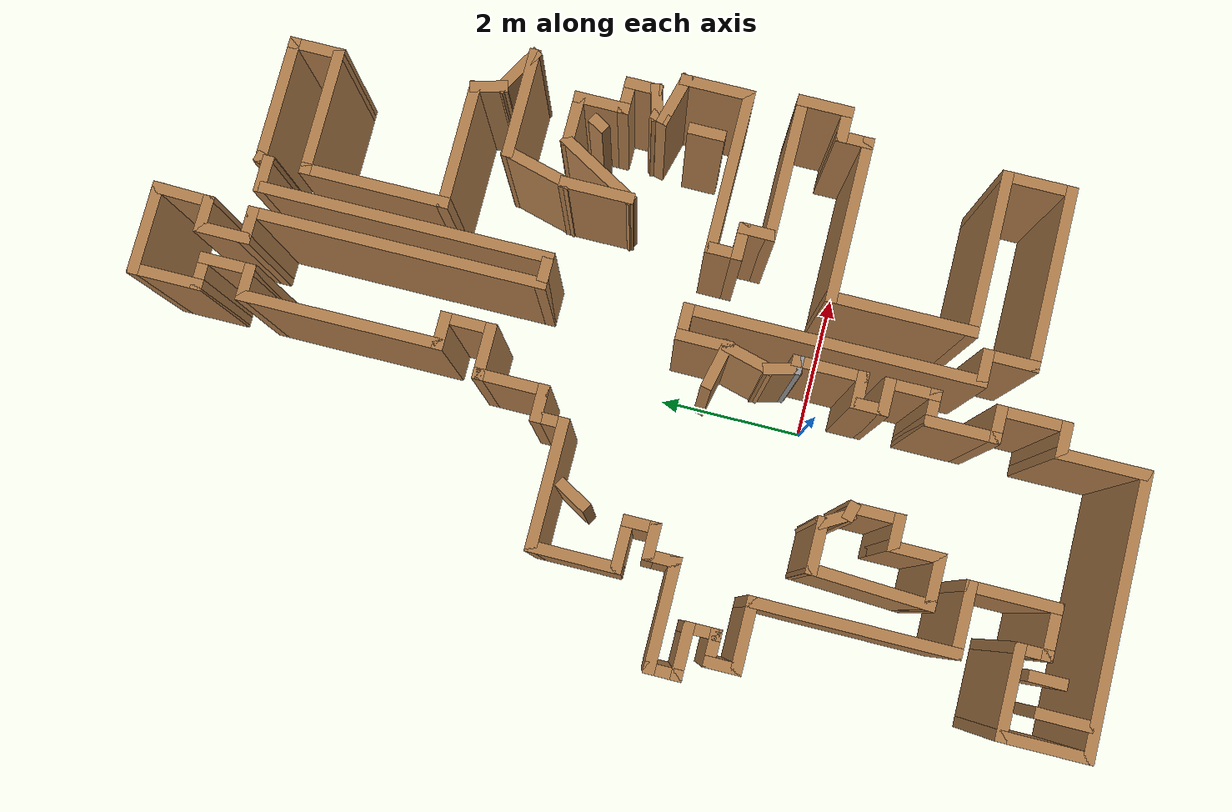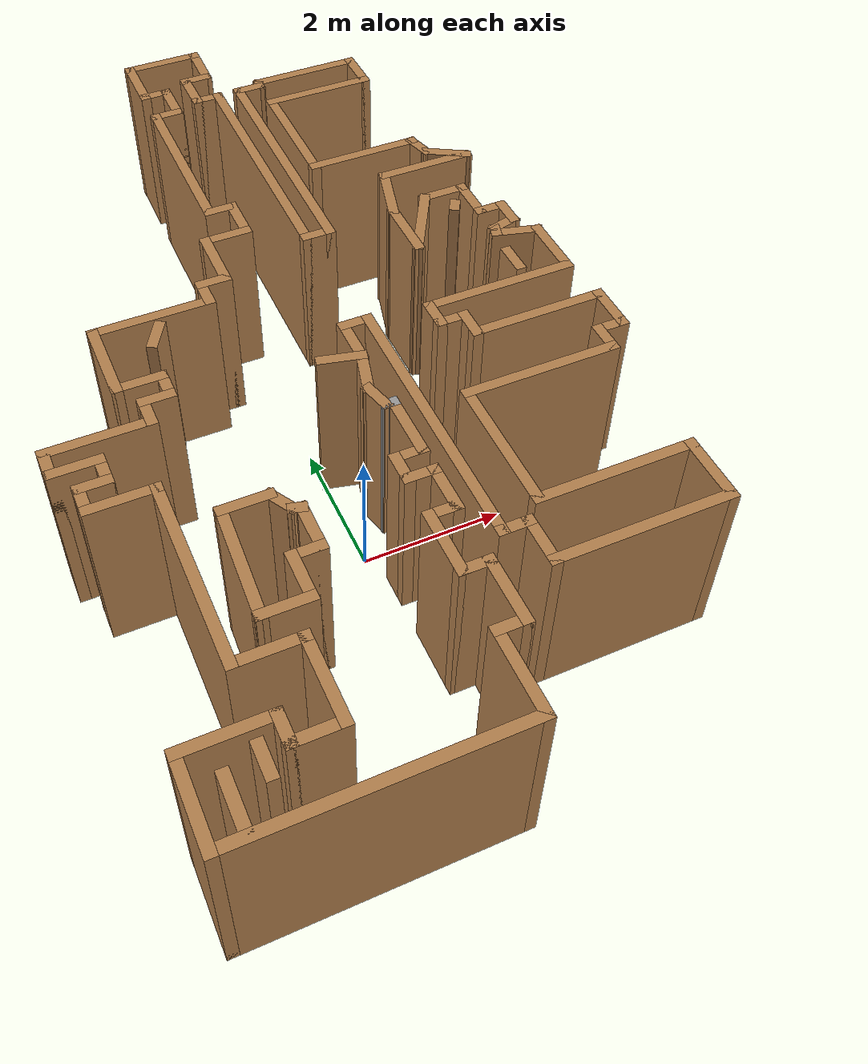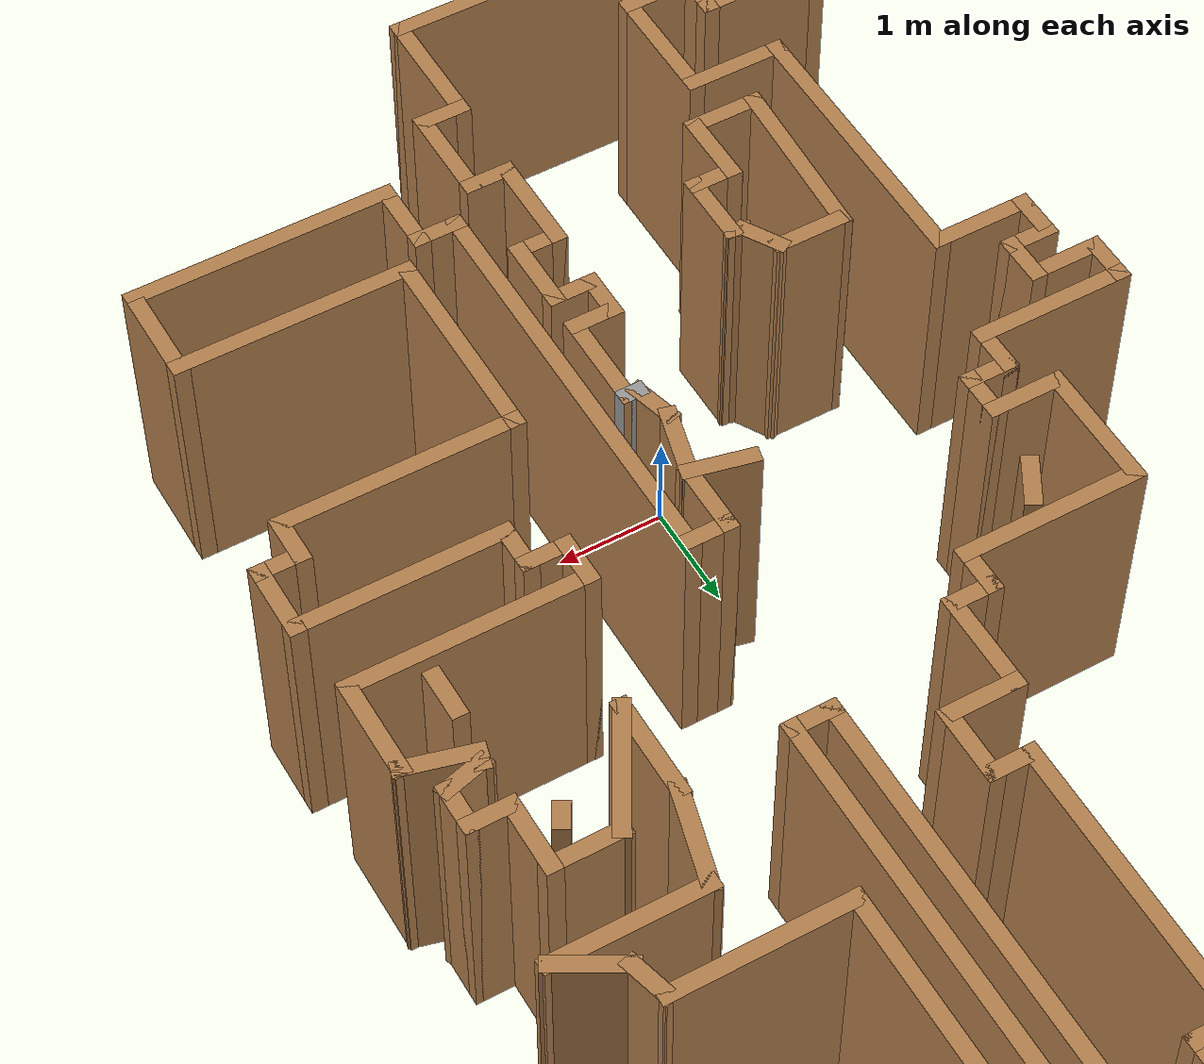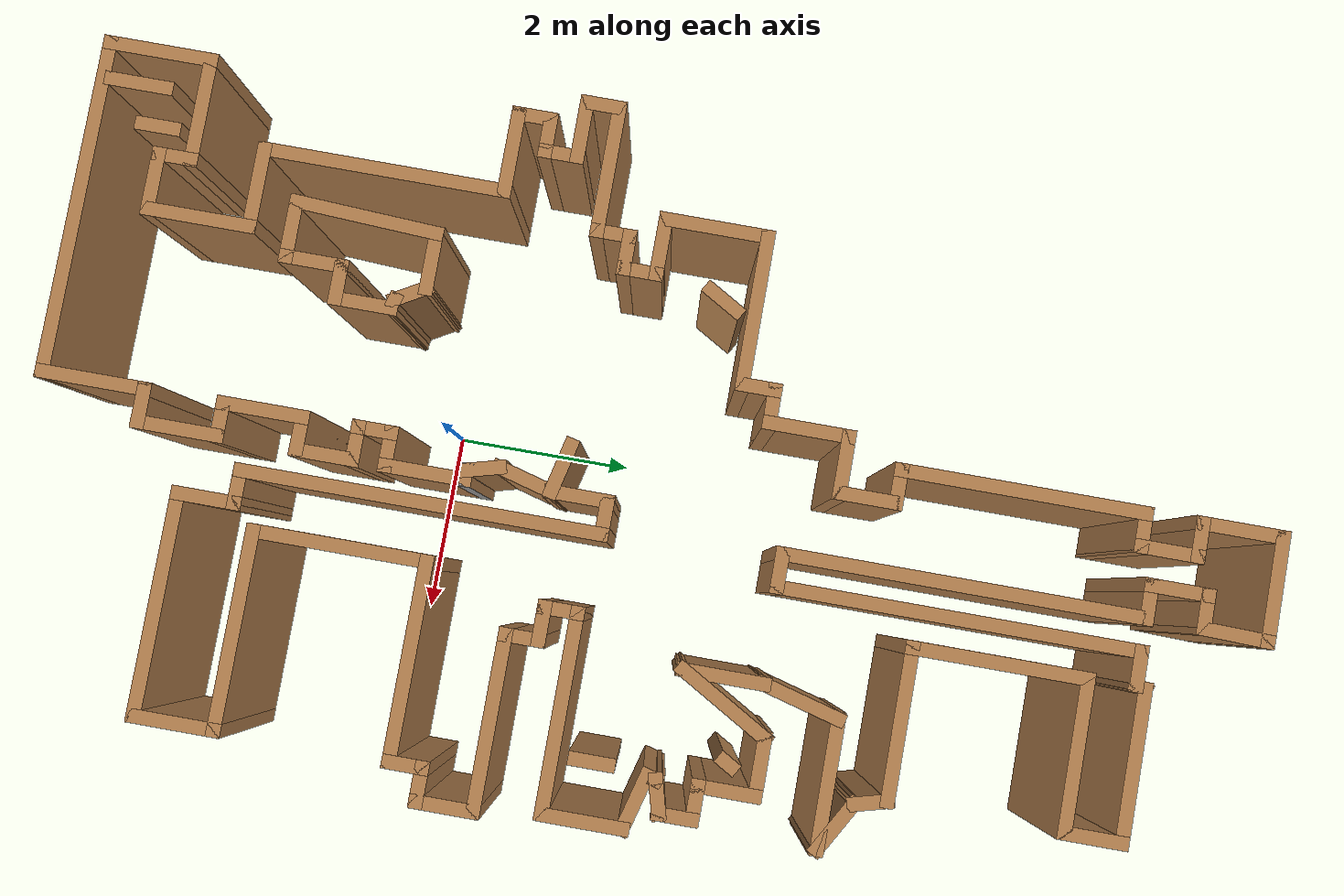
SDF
<?xml version='1.0'?>
<sdf version='1.6'>
  <model name='map_32'>
    <pose frame=''>0.162986 2.39573 0 0 -0 0</pose>
    <link name='Wall_10'>
      <collision name='Wall_10_Collision'>
        <geometry>
          <box>
            <size>0.75 0.15 2.5</size>
          </box>
        </geometry>
        <pose frame=''>0 0 1.25 0 -0 0</pose>
      </collision>
      <visual name='Wall_10_Visual'>
        <pose frame=''>0 0 1.25 0 -0 0</pose>
        <geometry>
          <box>
            <size>0.75 0.15 2.5</size>
          </box>
        </geometry>
        <material>
          <script>
            <uri>file://media/materials/scripts/gazebo.material</uri>
            <name>Gazebo/Wood</name>
          </script>
          <ambient>1 1 1 1</ambient>
        </material>
        <meta>
          <layer>0</layer>
        </meta>
      </visual>
      <pose frame=''>-0.432352 1.92407 0 0 -0 3.14159</pose>
    </link>
    <link name='Wall_103'>
      <collision name='Wall_103_Collision'>
        <geometry>
          <box>
            <size>1.75 0.15 2.5</size>
          </box>
        </geometry>
        <pose frame=''>0 0 1.25 0 -0 0</pose>
      </collision>
      <visual name='Wall_103_Visual'>
        <pose frame=''>0 0 1.25 0 -0 0</pose>
        <geometry>
          <box>
            <size>1.75 0.15 2.5</size>
          </box>
        </geometry>
        <material>
          <script>
            <uri>file://media/materials/scripts/gazebo.material</uri>
            <name>Gazebo/Wood</name>
          </script>
          <ambient>1 1 1 1</ambient>
        </material>
        <meta>
          <layer>0</layer>
        </meta>
      </visual>
      <pose frame=''>2.12655 5.39066 0 0 -0 3.14159</pose>
    </link>
    <link name='Wall_104'>
      <collision name='Wall_104_Collision'>
        <geometry>
          <box>
            <size>0.25 0.15 2.5</size>
          </box>
        </geometry>
        <pose frame=''>0 0 1.25 0 -0 0</pose>
      </collision>
      <visual name='Wall_104_Visual'>
        <pose frame=''>0 0 1.25 0 -0 0</pose>
        <geometry>
          <box>
            <size>0.25 0.15 2.5</size>
          </box>
        </geometry>
        <material>
          <script>
            <uri>file://media/materials/scripts/gazebo.material</uri>
            <name>Gazebo/Wood</name>
          </script>
          <ambient>1 1 1 1</ambient>
        </material>
        <meta>
          <layer>0</layer>
        </meta>
      </visual>
      <pose frame=''>1.31361 5.34236 0 0 -0 -1.8326</pose>
    </link>
    <link name='Wall_105'>
      <collision name='Wall_105_Collision'>
        <geometry>
          <box>
            <size>0.5 0.15 2.5</size>
          </box>
        </geometry>
        <pose frame=''>0 0 1.25 0 -0 0</pose>
      </collision>
      <visual name='Wall_105_Visual'>
        <pose frame=''>0 0 1.25 0 -0 0</pose>
        <geometry>
          <box>
            <size>0.5 0.15 2.5</size>
          </box>
        </geometry>
        <material>
          <script>
            <uri>file://media/materials/scripts/gazebo.material</uri>
            <name>Gazebo/Wood</name>
          </script>
          <ambient>1 1 1 1</ambient>
        </material>
        <meta>
          <layer>0</layer>
        </meta>
      </visual>
      <pose frame=''>1.12566 5.29407 0 0 -0 3.14159</pose>
    </link>
    <link name='Wall_106'>
      <collision name='Wall_106_Collision'>
        <geometry>
          <box>
            <size>4 0.15 2.5</size>
          </box>
        </geometry>
        <pose frame=''>0 0 1.25 0 -0 0</pose>
      </collision>
      <visual name='Wall_106_Visual'>
        <pose frame=''>0 0 1.25 0 -0 0</pose>
        <geometry>
          <box>
            <size>4 0.15 2.5</size>
          </box>
        </geometry>
        <material>
          <script>
            <uri>file://media/materials/scripts/gazebo.material</uri>
            <name>Gazebo/Wood</name>
          </script>
          <ambient>1 1 1 1</ambient>
        </material>
        <meta>
          <layer>0</layer>
        </meta>
      </visual>
      <pose frame=''>0.950665 3.36907 0 0 -0 -1.5708</pose>
    </link>
    <link name='Wall_107'>
      <collision name='Wall_107_Collision'>
        <geometry>
          <box>
            <size>0.5 0.15 2.5</size>
          </box>
        </geometry>
        <pose frame=''>0 0 1.25 0 -0 0</pose>
      </collision>
      <visual name='Wall_107_Visual'>
        <pose frame=''>0 0 1.25 0 -0 0</pose>
        <geometry>
          <box>
            <size>0.5 0.15 2.5</size>
          </box>
        </geometry>
        <material>
          <script>
            <uri>file://media/materials/scripts/gazebo.material</uri>
            <name>Gazebo/Wood</name>
          </script>
          <ambient>1 1 1 1</ambient>
        </material>
        <meta>
          <layer>0</layer>
        </meta>
      </visual>
      <pose frame=''>0.775665 1.44407 0 0 -0 3.14159</pose>
    </link>
    <link name='Wall_108'>
      <collision name='Wall_108_Collision'>
        <geometry>
          <box>
            <size>4 0.15 2.5</size>
          </box>
        </geometry>
        <pose frame=''>0 0 1.25 0 -0 0</pose>
      </collision>
      <visual name='Wall_108_Visual'>
        <pose frame=''>0 0 1.25 0 -0 0</pose>
        <geometry>
          <box>
            <size>4 0.15 2.5</size>
          </box>
        </geometry>
        <material>
          <script>
            <uri>file://media/materials/scripts/gazebo.material</uri>
            <name>Gazebo/Wood</name>
          </script>
          <ambient>1 1 1 1</ambient>
        </material>
        <meta>
          <layer>0</layer>
        </meta>
      </visual>
      <pose frame=''>0.600665 3.36907 0 0 -0 1.5708</pose>
    </link>
    <link name='Wall_109'>
      <collision name='Wall_109_Collision'>
        <geometry>
          <box>
            <size>0.5 0.15 2.5</size>
          </box>
        </geometry>
        <pose frame=''>0 0 1.25 0 -0 0</pose>
      </collision>
      <visual name='Wall_109_Visual'>
        <pose frame=''>0 0 1.25 0 -0 0</pose>
        <geometry>
          <box>
            <size>0.5 0.15 2.5</size>
          </box>
        </geometry>
        <material>
          <script>
            <uri>file://media/materials/scripts/gazebo.material</uri>
            <name>Gazebo/Wood</name>
          </script>
          <ambient>1 1 1 1</ambient>
        </material>
        <meta>
          <layer>0</layer>
        </meta>
      </visual>
      <pose frame=''>0.425665 5.29407 0 0 -0 3.14159</pose>
    </link>
    <link name='Wall_11'>
      <collision name='Wall_11_Collision'>
        <geometry>
          <box>
            <size>1 0.15 2.5</size>
          </box>
        </geometry>
        <pose frame=''>0 0 1.25 0 -0 0</pose>
      </collision>
      <visual name='Wall_11_Visual'>
        <pose frame=''>0 0 1.25 0 -0 0</pose>
        <geometry>
          <box>
            <size>1 0.15 2.5</size>
          </box>
        </geometry>
        <material>
          <script>
            <uri>file://media/materials/scripts/gazebo.material</uri>
            <name>Gazebo/Wood</name>
          </script>
          <ambient>1 1 1 1</ambient>
        </material>
        <meta>
          <layer>0</layer>
        </meta>
      </visual>
      <pose frame=''>-0.732352 1.49907 0 0 -0 -1.5708</pose>
    </link>
    <link name='Wall_110'>
      <collision name='Wall_110_Collision'>
        <geometry>
          <box>
            <size>0.75 0.15 2.5</size>
          </box>
        </geometry>
        <pose frame=''>0 0 1.25 0 -0 0</pose>
      </collision>
      <visual name='Wall_110_Visual'>
        <pose frame=''>0 0 1.25 0 -0 0</pose>
        <geometry>
          <box>
            <size>0.75 0.15 2.5</size>
          </box>
        </geometry>
        <material>
          <script>
            <uri>file://media/materials/scripts/gazebo.material</uri>
            <name>Gazebo/Wood</name>
          </script>
          <ambient>1 1 1 1</ambient>
        </material>
        <meta>
          <layer>0</layer>
        </meta>
      </visual>
      <pose frame=''>0.250665 5.59407 0 0 -0 1.5708</pose>
    </link>
    <link name='Wall_111'>
      <collision name='Wall_111_Collision'>
        <geometry>
          <box>
            <size>0.5 0.15 2.5</size>
          </box>
        </geometry>
        <pose frame=''>0 0 1.25 0 -0 0</pose>
      </collision>
      <visual name='Wall_111_Visual'>
        <pose frame=''>0 0 1.25 0 -0 0</pose>
        <geometry>
          <box>
            <size>0.5 0.15 2.5</size>
          </box>
        </geometry>
        <material>
          <script>
            <uri>file://media/materials/scripts/gazebo.material</uri>
            <name>Gazebo/Wood</name>
          </script>
          <ambient>1 1 1 1</ambient>
        </material>
        <meta>
          <layer>0</layer>
        </meta>
      </visual>
      <pose frame=''>0.425665 5.89407 0 0 -0 0</pose>
    </link>
    <link name='Wall_112'>
      <collision name='Wall_112_Collision'>
        <geometry>
          <box>
            <size>0.830221 0.15 2.5</size>
          </box>
        </geometry>
        <pose frame=''>0 0 1.25 0 -0 0</pose>
      </collision>
      <visual name='Wall_112_Visual'>
        <pose frame=''>0 0 1.25 0 -0 0</pose>
        <geometry>
          <box>
            <size>0.830221 0.15 2.5</size>
          </box>
        </geometry>
        <material>
          <script>
            <uri>file://media/materials/scripts/gazebo.material</uri>
            <name>Gazebo/Wood</name>
          </script>
          <ambient>1 1 1 1</ambient>
        </material>
        <meta>
          <layer>0</layer>
        </meta>
      </visual>
      <pose frame=''>0.609156 6.23407 0 0 -0 1.54583</pose>
    </link>
    <link name='Wall_116'>
      <collision name='Wall_116_Collision'>
        <geometry>
          <box>
            <size>0.5 0.15 2.5</size>
          </box>
        </geometry>
        <pose frame=''>0 0 1.25 0 -0 0</pose>
      </collision>
      <visual name='Wall_116_Visual'>
        <pose frame=''>0 0 1.25 0 -0 0</pose>
        <geometry>
          <box>
            <size>0.5 0.15 2.5</size>
          </box>
        </geometry>
        <material>
          <script>
            <uri>file://media/materials/scripts/gazebo.material</uri>
            <name>Gazebo/Wood</name>
          </script>
          <ambient>1 1 1 1</ambient>
        </material>
        <meta>
          <layer>0</layer>
        </meta>
      </visual>
      <pose frame=''>3.06584 -0.141038 0 0 -0 1.5708</pose>
    </link>
    <link name='Wall_119'>
      <collision name='Wall_119_Collision'>
        <geometry>
          <box>
            <size>0.25 0.15 2.5</size>
          </box>
        </geometry>
        <pose frame=''>0 0 1.25 0 -0 0</pose>
      </collision>
      <visual name='Wall_119_Visual'>
        <pose frame=''>0 0 1.25 0 -0 0</pose>
        <geometry>
          <box>
            <size>0.25 0.15 2.5</size>
          </box>
        </geometry>
        <material>
          <script>
            <uri>file://media/materials/scripts/gazebo.material</uri>
            <name>Gazebo/Wood</name>
          </script>
          <ambient>1 1 1 1</ambient>
        </material>
        <meta>
          <layer>0</layer>
        </meta>
      </visual>
      <pose frame=''>2.83971 1.24975 0 0 -0 -2.0944</pose>
    </link>
    <link name='Wall_121'>
      <collision name='Wall_121_Collision'>
        <geometry>
          <box>
            <size>0.5 0.15 2.5</size>
          </box>
        </geometry>
        <pose frame=''>0 0 1.25 0 -0 0</pose>
      </collision>
      <visual name='Wall_121_Visual'>
        <pose frame=''>0 0 1.25 0 -0 0</pose>
        <geometry>
          <box>
            <size>0.5 0.15 2.5</size>
          </box>
        </geometry>
        <material>
          <script>
            <uri>file://media/materials/scripts/gazebo.material</uri>
            <name>Gazebo/Wood</name>
          </script>
          <ambient>1 1 1 1</ambient>
        </material>
        <meta>
          <layer>0</layer>
        </meta>
      </visual>
      <pose frame=''>-1.92937 0.377178 0 0 -0 -2.0944</pose>
    </link>
    <link name='Wall_123'>
      <collision name='Wall_123_Collision'>
        <geometry>
          <box>
            <size>0.678088 0.15 2.5</size>
          </box>
        </geometry>
        <pose frame=''>0 0 1.25 0 -0 0</pose>
      </collision>
      <visual name='Wall_123_Visual'>
        <pose frame=''>0 0 1.25 0 -0 0</pose>
        <geometry>
          <box>
            <size>0.678088 0.15 2.5</size>
          </box>
        </geometry>
        <material>
          <script>
            <uri>file://media/materials/scripts/gazebo.material</uri>
            <name>Gazebo/Wood</name>
          </script>
          <ambient>1 1 1 1</ambient>
        </material>
        <meta>
          <layer>0</layer>
        </meta>
      </visual>
      <pose frame=''>0.125069 -0.998927 0 0 -0 -0.226782</pose>
    </link>
    <link name='Wall_130'>
      <collision name='Wall_130_Collision'>
        <geometry>
          <box>
            <size>0.75 0.15 2.5</size>
          </box>
        </geometry>
        <pose frame=''>0 0 1.25 0 -0 0</pose>
      </collision>
      <visual name='Wall_130_Visual'>
        <pose frame=''>0 0 1.25 0 -0 0</pose>
        <geometry>
          <box>
            <size>0.75 0.15 2.5</size>
          </box>
        </geometry>
        <material>
          <script>
            <uri>file://media/materials/scripts/gazebo.material</uri>
            <name>Gazebo/Wood</name>
          </script>
          <ambient>1 1 1 1</ambient>
        </material>
        <meta>
          <layer>0</layer>
        </meta>
      </visual>
      <pose frame=''>-1.8838 -4.27841 0 0 -0 0</pose>
    </link>
    <link name='Wall_131'>
      <collision name='Wall_131_Collision'>
        <geometry>
          <box>
            <size>0.75 0.15 2.5</size>
          </box>
        </geometry>
        <pose frame=''>0 0 1.25 0 -0 0</pose>
      </collision>
      <visual name='Wall_131_Visual'>
        <pose frame=''>0 0 1.25 0 -0 0</pose>
        <geometry>
          <box>
            <size>0.75 0.15 2.5</size>
          </box>
        </geometry>
        <material>
          <script>
            <uri>file://media/materials/scripts/gazebo.material</uri>
            <name>Gazebo/Wood</name>
          </script>
          <ambient>1 1 1 1</ambient>
        </material>
        <meta>
          <layer>0</layer>
        </meta>
      </visual>
      <pose frame=''>-1.5838 -3.97841 0 0 -0 1.5708</pose>
    </link>
    <link name='Wall_132'>
      <collision name='Wall_132_Collision'>
        <geometry>
          <box>
            <size>0.5 0.15 2.5</size>
          </box>
        </geometry>
        <pose frame=''>0 0 1.25 0 -0 0</pose>
      </collision>
      <visual name='Wall_132_Visual'>
        <pose frame=''>0 0 1.25 0 -0 0</pose>
        <geometry>
          <box>
            <size>0.5 0.15 2.5</size>
          </box>
        </geometry>
        <material>
          <script>
            <uri>file://media/materials/scripts/gazebo.material</uri>
            <name>Gazebo/Wood</name>
          </script>
          <ambient>1 1 1 1</ambient>
        </material>
        <meta>
          <layer>0</layer>
        </meta>
      </visual>
      <pose frame=''>-1.4088 -3.67841 0 0 -0 0</pose>
    </link>
    <link name='Wall_133'>
      <collision name='Wall_133_Collision'>
        <geometry>
          <box>
            <size>0.75 0.15 2.5</size>
          </box>
        </geometry>
        <pose frame=''>0 0 1.25 0 -0 0</pose>
      </collision>
      <visual name='Wall_133_Visual'>
        <pose frame=''>0 0 1.25 0 -0 0</pose>
        <geometry>
          <box>
            <size>0.75 0.15 2.5</size>
          </box>
        </geometry>
        <material>
          <script>
            <uri>file://media/materials/scripts/gazebo.material</uri>
            <name>Gazebo/Wood</name>
          </script>
          <ambient>1 1 1 1</ambient>
        </material>
        <meta>
          <layer>0</layer>
        </meta>
      </visual>
      <pose frame=''>-1.2338 -3.37841 0 0 -0 1.5708</pose>
    </link>
    <link name='Wall_134'>
      <collision name='Wall_134_Collision'>
        <geometry>
          <box>
            <size>0.25 0.15 2.5</size>
          </box>
        </geometry>
        <pose frame=''>0 0 1.25 0 -0 0</pose>
      </collision>
      <visual name='Wall_134_Visual'>
        <pose frame=''>0 0 1.25 0 -0 0</pose>
        <geometry>
          <box>
            <size>0.25 0.15 2.5</size>
          </box>
        </geometry>
        <material>
          <script>
            <uri>file://media/materials/scripts/gazebo.material</uri>
            <name>Gazebo/Wood</name>
          </script>
          <ambient>1 1 1 1</ambient>
        </material>
        <meta>
          <layer>0</layer>
        </meta>
      </visual>
      <pose frame=''>-1.28209 -3.06547 0 0 -0 2.87979</pose>
    </link>
    <link name='Wall_135'>
      <collision name='Wall_135_Collision'>
        <geometry>
          <box>
            <size>0.5 0.15 2.5</size>
          </box>
        </geometry>
        <pose frame=''>0 0 1.25 0 -0 0</pose>
      </collision>
      <visual name='Wall_135_Visual'>
        <pose frame=''>0 0 1.25 0 -0 0</pose>
        <geometry>
          <box>
            <size>0.5 0.15 2.5</size>
          </box>
        </geometry>
        <material>
          <script>
            <uri>file://media/materials/scripts/gazebo.material</uri>
            <name>Gazebo/Wood</name>
          </script>
          <ambient>1 1 1 1</ambient>
        </material>
        <meta>
          <layer>0</layer>
        </meta>
      </visual>
      <pose frame=''>-1.41789 -2.90097 0 0 -0 2.0944</pose>
    </link>
    <link name='Wall_136'>
      <collision name='Wall_136_Collision'>
        <geometry>
          <box>
            <size>0.75 0.15 2.5</size>
          </box>
        </geometry>
        <pose frame=''>0 0 1.25 0 -0 0</pose>
      </collision>
      <visual name='Wall_136_Visual'>
        <pose frame=''>0 0 1.25 0 -0 0</pose>
        <geometry>
          <box>
            <size>0.75 0.15 2.5</size>
          </box>
        </geometry>
        <material>
          <script>
            <uri>file://media/materials/scripts/gazebo.material</uri>
            <name>Gazebo/Wood</name>
          </script>
          <ambient>1 1 1 1</ambient>
        </material>
        <meta>
          <layer>0</layer>
        </meta>
      </visual>
      <pose frame=''>-1.80539 -2.74942 0 0 -0 3.14159</pose>
    </link>
    <link name='Wall_137'>
      <collision name='Wall_137_Collision'>
        <geometry>
          <box>
            <size>1.681 0.15 2.5</size>
          </box>
        </geometry>
        <pose frame=''>0 0 1.25 0 -0 0</pose>
      </collision>
      <visual name='Wall_137_Visual'>
        <pose frame=''>0 0 1.25 0 -0 0</pose>
        <geometry>
          <box>
            <size>1.681 0.15 2.5</size>
          </box>
        </geometry>
        <material>
          <script>
            <uri>file://media/materials/scripts/gazebo.material</uri>
            <name>Gazebo/Wood</name>
          </script>
          <ambient>1 1 1 1</ambient>
        </material>
        <meta>
          <layer>0</layer>
        </meta>
      </visual>
      <pose frame=''>-2.14459 -3.51392 0 0 -0 -1.62203</pose>
    </link>
    <link name='Wall_139'>
      <collision name='Wall_139_Collision'>
        <geometry>
          <box>
            <size>0.75 0.15 2.5</size>
          </box>
        </geometry>
        <pose frame=''>0 0 1.25 0 -0 0</pose>
      </collision>
      <visual name='Wall_139_Visual'>
        <pose frame=''>0 0 1.25 0 -0 0</pose>
        <geometry>
          <box>
            <size>0.75 0.15 2.5</size>
          </box>
        </geometry>
        <material>
          <script>
            <uri>file://media/materials/scripts/gazebo.material</uri>
            <name>Gazebo/Wood</name>
          </script>
          <ambient>1 1 1 1</ambient>
        </material>
        <meta>
          <layer>0</layer>
        </meta>
      </visual>
      <pose frame=''>-3.14925 -6.1875 0 0 -0 -1.5708</pose>
    </link>
    <link name='Wall_14'>
      <collision name='Wall_14_Collision'>
        <geometry>
          <box>
            <size>0.5 0.15 2.5</size>
          </box>
        </geometry>
        <pose frame=''>0 0 1.25 0 -0 0</pose>
      </collision>
      <visual name='Wall_14_Visual'>
        <pose frame=''>0 0 1.25 0 -0 0</pose>
        <geometry>
          <box>
            <size>0.5 0.15 2.5</size>
          </box>
        </geometry>
        <material>
          <script>
            <uri>file://media/materials/scripts/gazebo.material</uri>
            <name>Gazebo/Wood</name>
          </script>
          <ambient>1 1 1 1</ambient>
        </material>
        <meta>
          <layer>0</layer>
        </meta>
      </visual>
      <pose frame=''>-0.907352 1.07407 0 0 -0 3.14159</pose>
    </link>
    <link name='Wall_142'>
      <collision name='Wall_142_Collision'>
        <geometry>
          <box>
            <size>0.5 0.15 2.5</size>
          </box>
        </geometry>
        <pose frame=''>0 0 1.25 0 -0 0</pose>
      </collision>
      <visual name='Wall_142_Visual'>
        <pose frame=''>0 0 1.25 0 -0 0</pose>
        <geometry>
          <box>
            <size>0.5 0.15 2.5</size>
          </box>
        </geometry>
        <material>
          <script>
            <uri>file://media/materials/scripts/gazebo.material</uri>
            <name>Gazebo/Wood</name>
          </script>
          <ambient>1 1 1 1</ambient>
        </material>
        <meta>
          <layer>0</layer>
        </meta>
      </visual>
      <pose frame=''>-2.72686 -5.89352 0 0 -0 1.5708</pose>
    </link>
    <link name='Wall_15'>
      <collision name='Wall_15_Collision'>
        <geometry>
          <box>
            <size>0.5 0.15 2.5</size>
          </box>
        </geometry>
        <pose frame=''>0 0 1.25 0 -0 0</pose>
      </collision>
      <visual name='Wall_15_Visual'>
        <pose frame=''>0 0 1.25 0 -0 0</pose>
        <geometry>
          <box>
            <size>0.5 0.15 2.5</size>
          </box>
        </geometry>
        <material>
          <script>
            <uri>file://media/materials/scripts/gazebo.material</uri>
            <name>Gazebo/Wood</name>
          </script>
          <ambient>1 1 1 1</ambient>
        </material>
        <meta>
          <layer>0</layer>
        </meta>
      </visual>
      <pose frame=''>-1.08235 0.899075 0 0 -0 -1.5708</pose>
    </link>
    <link name='Wall_18'>
      <collision name='Wall_18_Collision'>
        <geometry>
          <box>
            <size>1.75 0.15 2.5</size>
          </box>
        </geometry>
        <pose frame=''>0 0 1.25 0 -0 0</pose>
      </collision>
      <visual name='Wall_18_Visual'>
        <pose frame=''>0 0 1.25 0 -0 0</pose>
        <geometry>
          <box>
            <size>1.75 0.15 2.5</size>
          </box>
        </geometry>
        <material>
          <script>
            <uri>file://media/materials/scripts/gazebo.material</uri>
            <name>Gazebo/Wood</name>
          </script>
          <ambient>1 1 1 1</ambient>
        </material>
        <meta>
          <layer>0</layer>
        </meta>
      </visual>
      <pose frame=''>-1.88235 0.724075 0 0 -0 3.14159</pose>
    </link>
    <link name='Wall_19'>
      <collision name='Wall_19_Collision'>
        <geometry>
          <box>
            <size>1.25 0.15 2.5</size>
          </box>
        </geometry>
        <pose frame=''>0 0 1.25 0 -0 0</pose>
      </collision>
      <visual name='Wall_19_Visual'>
        <pose frame=''>0 0 1.25 0 -0 0</pose>
        <geometry>
          <box>
            <size>1.25 0.15 2.5</size>
          </box>
        </geometry>
        <material>
          <script>
            <uri>file://media/materials/scripts/gazebo.material</uri>
            <name>Gazebo/Wood</name>
          </script>
          <ambient>1 1 1 1</ambient>
        </material>
        <meta>
          <layer>0</layer>
        </meta>
      </visual>
      <pose frame=''>-2.68235 0.174075 0 0 -0 -1.5708</pose>
    </link>
    <link name='Wall_2'>
      <collision name='Wall_2_Collision'>
        <geometry>
          <box>
            <size>1.25 0.15 2.5</size>
          </box>
        </geometry>
        <pose frame=''>0 0 1.25 0 -0 0</pose>
      </collision>
      <visual name='Wall_2_Visual'>
        <pose frame=''>0 0 1.25 0 -0 0</pose>
        <geometry>
          <box>
            <size>1.25 0.15 2.5</size>
          </box>
        </geometry>
        <material>
          <script>
            <uri>file://media/materials/scripts/gazebo.material</uri>
            <name>Gazebo/Wood</name>
          </script>
          <ambient>1 1 1 1</ambient>
        </material>
        <meta>
          <layer>0</layer>
        </meta>
      </visual>
      <pose frame=''>0.067648 6.57408 0 0 -0 3.14159</pose>
    </link>
    <link name='Wall_20'>
      <collision name='Wall_20_Collision'>
        <geometry>
          <box>
            <size>0.75 0.15 2.5</size>
          </box>
        </geometry>
        <pose frame=''>0 0 1.25 0 -0 0</pose>
      </collision>
      <visual name='Wall_20_Visual'>
        <pose frame=''>0 0 1.25 0 -0 0</pose>
        <geometry>
          <box>
            <size>0.75 0.15 2.5</size>
          </box>
        </geometry>
        <material>
          <script>
            <uri>file://media/materials/scripts/gazebo.material</uri>
            <name>Gazebo/Wood</name>
          </script>
          <ambient>1 1 1 1</ambient>
        </material>
        <meta>
          <layer>0</layer>
        </meta>
      </visual>
      <pose frame=''>-2.38235 -0.375925 0 0 -0 0</pose>
    </link>
    <link name='Wall_21'>
      <collision name='Wall_21_Collision'>
        <geometry>
          <box>
            <size>0.5 0.15 2.5</size>
          </box>
        </geometry>
        <pose frame=''>0 0 1.25 0 -0 0</pose>
      </collision>
      <visual name='Wall_21_Visual'>
        <pose frame=''>0 0 1.25 0 -0 0</pose>
        <geometry>
          <box>
            <size>0.5 0.15 2.5</size>
          </box>
        </geometry>
        <material>
          <script>
            <uri>file://media/materials/scripts/gazebo.material</uri>
            <name>Gazebo/Wood</name>
          </script>
          <ambient>1 1 1 1</ambient>
        </material>
        <meta>
          <layer>0</layer>
        </meta>
      </visual>
      <pose frame=''>-2.08235 -0.550925 0 0 -0 -1.5708</pose>
    </link>
    <link name='Wall_22'>
      <collision name='Wall_22_Collision'>
        <geometry>
          <box>
            <size>0.5 0.15 2.5</size>
          </box>
        </geometry>
        <pose frame=''>0 0 1.25 0 -0 0</pose>
      </collision>
      <visual name='Wall_22_Visual'>
        <pose frame=''>0 0 1.25 0 -0 0</pose>
        <geometry>
          <box>
            <size>0.5 0.15 2.5</size>
          </box>
        </geometry>
        <material>
          <script>
            <uri>file://media/materials/scripts/gazebo.material</uri>
            <name>Gazebo/Wood</name>
          </script>
          <ambient>1 1 1 1</ambient>
        </material>
        <meta>
          <layer>0</layer>
        </meta>
      </visual>
      <pose frame=''>-2.25735 -0.725925 0 0 -0 3.14159</pose>
    </link>
    <link name='Wall_23'>
      <collision name='Wall_23_Collision'>
        <geometry>
          <box>
            <size>0.5 0.15 2.5</size>
          </box>
        </geometry>
        <pose frame=''>0 0 1.25 0 -0 0</pose>
      </collision>
      <visual name='Wall_23_Visual'>
        <pose frame=''>0 0 1.25 0 -0 0</pose>
        <geometry>
          <box>
            <size>0.5 0.15 2.5</size>
          </box>
        </geometry>
        <material>
          <script>
            <uri>file://media/materials/scripts/gazebo.material</uri>
            <name>Gazebo/Wood</name>
          </script>
          <ambient>1 1 1 1</ambient>
        </material>
        <meta>
          <layer>0</layer>
        </meta>
      </visual>
      <pose frame=''>-2.43235 -0.900925 0 0 -0 -1.5708</pose>
    </link>
    <link name='Wall_24'>
      <collision name='Wall_24_Collision'>
        <geometry>
          <box>
            <size>1.5 0.15 2.5</size>
          </box>
        </geometry>
        <pose frame=''>0 0 1.25 0 -0 0</pose>
      </collision>
      <visual name='Wall_24_Visual'>
        <pose frame=''>0 0 1.25 0 -0 0</pose>
        <geometry>
          <box>
            <size>1.5 0.15 2.5</size>
          </box>
        </geometry>
        <material>
          <script>
            <uri>file://media/materials/scripts/gazebo.material</uri>
            <name>Gazebo/Wood</name>
          </script>
          <ambient>1 1 1 1</ambient>
        </material>
        <meta>
          <layer>0</layer>
        </meta>
      </visual>
      <pose frame=''>-3.10735 -1.07593 0 0 -0 3.14159</pose>
    </link>
    <link name='Wall_27'>
      <collision name='Wall_27_Collision'>
        <geometry>
          <box>
            <size>0.5 0.15 2.5</size>
          </box>
        </geometry>
        <pose frame=''>0 0 1.25 0 -0 0</pose>
      </collision>
      <visual name='Wall_27_Visual'>
        <pose frame=''>0 0 1.25 0 -0 0</pose>
        <geometry>
          <box>
            <size>0.5 0.15 2.5</size>
          </box>
        </geometry>
        <material>
          <script>
            <uri>file://media/materials/scripts/gazebo.material</uri>
            <name>Gazebo/Wood</name>
          </script>
          <ambient>1 1 1 1</ambient>
        </material>
        <meta>
          <layer>0</layer>
        </meta>
      </visual>
      <pose frame=''>-3.78235 -1.25093 0 0 -0 -1.5708</pose>
    </link>
    <link name='Wall_28'>
      <collision name='Wall_28_Collision'>
        <geometry>
          <box>
            <size>0.75 0.15 2.5</size>
          </box>
        </geometry>
        <pose frame=''>0 0 1.25 0 -0 0</pose>
      </collision>
      <visual name='Wall_28_Visual'>
        <pose frame=''>0 0 1.25 0 -0 0</pose>
        <geometry>
          <box>
            <size>0.75 0.15 2.5</size>
          </box>
        </geometry>
        <material>
          <script>
            <uri>file://media/materials/scripts/gazebo.material</uri>
            <name>Gazebo/Wood</name>
          </script>
          <ambient>1 1 1 1</ambient>
        </material>
        <meta>
          <layer>0</layer>
        </meta>
      </visual>
      <pose frame=''>-3.48235 -1.42593 0 0 -0 0</pose>
    </link>
    <link name='Wall_29'>
      <collision name='Wall_29_Collision'>
        <geometry>
          <box>
            <size>0.5 0.15 2.5</size>
          </box>
        </geometry>
        <pose frame=''>0 0 1.25 0 -0 0</pose>
      </collision>
      <visual name='Wall_29_Visual'>
        <pose frame=''>0 0 1.25 0 -0 0</pose>
        <geometry>
          <box>
            <size>0.5 0.15 2.5</size>
          </box>
        </geometry>
        <material>
          <script>
            <uri>file://media/materials/scripts/gazebo.material</uri>
            <name>Gazebo/Wood</name>
          </script>
          <ambient>1 1 1 1</ambient>
        </material>
        <meta>
          <layer>0</layer>
        </meta>
      </visual>
      <pose frame=''>-3.18235 -1.60092 0 0 -0 -1.5708</pose>
    </link>
    <link name='Wall_3'>
      <collision name='Wall_3_Collision'>
        <geometry>
          <box>
            <size>1 0.15 2.5</size>
          </box>
        </geometry>
        <pose frame=''>0 0 1.25 0 -0 0</pose>
      </collision>
      <visual name='Wall_3_Visual'>
        <pose frame=''>0 0 1.25 0 -0 0</pose>
        <geometry>
          <box>
            <size>1 0.15 2.5</size>
          </box>
        </geometry>
        <material>
          <script>
            <uri>file://media/materials/scripts/gazebo.material</uri>
            <name>Gazebo/Wood</name>
          </script>
          <ambient>1 1 1 1</ambient>
        </material>
        <meta>
          <layer>0</layer>
        </meta>
      </visual>
      <pose frame=''>-0.482352 6.14908 0 0 -0 -1.5708</pose>
    </link>
    <link name='Wall_30'>
      <collision name='Wall_30_Collision'>
        <geometry>
          <box>
            <size>0.5 0.15 2.5</size>
          </box>
        </geometry>
        <pose frame=''>0 0 1.25 0 -0 0</pose>
      </collision>
      <visual name='Wall_30_Visual'>
        <pose frame=''>0 0 1.25 0 -0 0</pose>
        <geometry>
          <box>
            <size>0.5 0.15 2.5</size>
          </box>
        </geometry>
        <material>
          <script>
            <uri>file://media/materials/scripts/gazebo.material</uri>
            <name>Gazebo/Wood</name>
          </script>
          <ambient>1 1 1 1</ambient>
        </material>
        <meta>
          <layer>0</layer>
        </meta>
      </visual>
      <pose frame=''>-3.35735 -1.77592 0 0 -0 3.14159</pose>
    </link>
    <link name='Wall_31'>
      <collision name='Wall_31_Collision'>
        <geometry>
          <box>
            <size>0.5 0.15 2.5</size>
          </box>
        </geometry>
        <pose frame=''>0 0 1.25 0 -0 0</pose>
      </collision>
      <visual name='Wall_31_Visual'>
        <pose frame=''>0 0 1.25 0 -0 0</pose>
        <geometry>
          <box>
            <size>0.5 0.15 2.5</size>
          </box>
        </geometry>
        <material>
          <script>
            <uri>file://media/materials/scripts/gazebo.material</uri>
            <name>Gazebo/Wood</name>
          </script>
          <ambient>1 1 1 1</ambient>
        </material>
        <meta>
          <layer>0</layer>
        </meta>
      </visual>
      <pose frame=''>-3.53235 -1.95093 0 0 -0 -1.5708</pose>
    </link>
    <link name='Wall_32'>
      <collision name='Wall_32_Collision'>
        <geometry>
          <box>
            <size>1 0.15 2.5</size>
          </box>
        </geometry>
        <pose frame=''>0 0 1.25 0 -0 0</pose>
      </collision>
      <visual name='Wall_32_Visual'>
        <pose frame=''>0 0 1.25 0 -0 0</pose>
        <geometry>
          <box>
            <size>1 0.15 2.5</size>
          </box>
        </geometry>
        <material>
          <script>
            <uri>file://media/materials/scripts/gazebo.material</uri>
            <name>Gazebo/Wood</name>
          </script>
          <ambient>1 1 1 1</ambient>
        </material>
        <meta>
          <layer>0</layer>
        </meta>
      </visual>
      <pose frame=''>-3.10735 -2.12593 0 0 -0 0</pose>
    </link>
    <link name='Wall_33'>
      <collision name='Wall_33_Collision'>
        <geometry>
          <box>
            <size>2.75 0.15 2.5</size>
          </box>
        </geometry>
        <pose frame=''>0 0 1.25 0 -0 0</pose>
      </collision>
      <visual name='Wall_33_Visual'>
        <pose frame=''>0 0 1.25 0 -0 0</pose>
        <geometry>
          <box>
            <size>2.75 0.15 2.5</size>
          </box>
        </geometry>
        <material>
          <script>
            <uri>file://media/materials/scripts/gazebo.material</uri>
            <name>Gazebo/Wood</name>
          </script>
          <ambient>1 1 1 1</ambient>
        </material>
        <meta>
          <layer>0</layer>
        </meta>
      </visual>
      <pose frame=''>-2.68235 -3.42592 0 0 -0 -1.5708</pose>
    </link>
    <link name='Wall_34'>
      <collision name='Wall_34_Collision'>
        <geometry>
          <box>
            <size>1 0.15 2.5</size>
          </box>
        </geometry>
        <pose frame=''>0 0 1.25 0 -0 0</pose>
      </collision>
      <visual name='Wall_34_Visual'>
        <pose frame=''>0 0 1.25 0 -0 0</pose>
        <geometry>
          <box>
            <size>1 0.15 2.5</size>
          </box>
        </geometry>
        <material>
          <script>
            <uri>file://media/materials/scripts/gazebo.material</uri>
            <name>Gazebo/Wood</name>
          </script>
          <ambient>1 1 1 1</ambient>
        </material>
        <meta>
          <layer>0</layer>
        </meta>
      </visual>
      <pose frame=''>-2.25735 -4.72593 0 0 -0 0</pose>
    </link>
    <link name='Wall_37'>
      <collision name='Wall_37_Collision'>
        <geometry>
          <box>
            <size>1.25 0.15 2.5</size>
          </box>
        </geometry>
        <pose frame=''>0 0 1.25 0 -0 0</pose>
      </collision>
      <visual name='Wall_37_Visual'>
        <pose frame=''>0 0 1.25 0 -0 0</pose>
        <geometry>
          <box>
            <size>1.25 0.15 2.5</size>
          </box>
        </geometry>
        <material>
          <script>
            <uri>file://media/materials/scripts/gazebo.material</uri>
            <name>Gazebo/Wood</name>
          </script>
          <ambient>1 1 1 1</ambient>
        </material>
        <meta>
          <layer>0</layer>
        </meta>
      </visual>
      <pose frame=''>-1.83235 -5.27592 0 0 -0 -1.5708</pose>
    </link>
    <link name='Wall_4'>
      <collision name='Wall_4_Collision'>
        <geometry>
          <box>
            <size>0.5 0.15 2.5</size>
          </box>
        </geometry>
        <pose frame=''>0 0 1.25 0 -0 0</pose>
      </collision>
      <visual name='Wall_4_Visual'>
        <pose frame=''>0 0 1.25 0 -0 0</pose>
        <geometry>
          <box>
            <size>0.5 0.15 2.5</size>
          </box>
        </geometry>
        <material>
          <script>
            <uri>file://media/materials/scripts/gazebo.material</uri>
            <name>Gazebo/Wood</name>
          </script>
          <ambient>1 1 1 1</ambient>
        </material>
        <meta>
          <layer>0</layer>
        </meta>
      </visual>
      <pose frame=''>-0.307352 5.72408 0 0 -0 0</pose>
    </link>
    <link name='Wall_40'>
      <collision name='Wall_40_Collision'>
        <geometry>
          <box>
            <size>0.75 0.15 2.5</size>
          </box>
        </geometry>
        <pose frame=''>0 0 1.25 0 -0 0</pose>
      </collision>
      <visual name='Wall_40_Visual'>
        <pose frame=''>0 0 1.25 0 -0 0</pose>
        <geometry>
          <box>
            <size>0.75 0.15 2.5</size>
          </box>
        </geometry>
        <material>
          <script>
            <uri>file://media/materials/scripts/gazebo.material</uri>
            <name>Gazebo/Wood</name>
          </script>
          <ambient>1 1 1 1</ambient>
        </material>
        <meta>
          <layer>0</layer>
        </meta>
      </visual>
      <pose frame=''>-2.13235 -5.82592 0 0 -0 3.14159</pose>
    </link>
    <link name='Wall_41'>
      <collision name='Wall_41_Collision'>
        <geometry>
          <box>
            <size>0.5 0.15 2.5</size>
          </box>
        </geometry>
        <pose frame=''>0 0 1.25 0 -0 0</pose>
      </collision>
      <visual name='Wall_41_Visual'>
        <pose frame=''>0 0 1.25 0 -0 0</pose>
        <geometry>
          <box>
            <size>0.5 0.15 2.5</size>
          </box>
        </geometry>
        <material>
          <script>
            <uri>file://media/materials/scripts/gazebo.material</uri>
            <name>Gazebo/Wood</name>
          </script>
          <ambient>1 1 1 1</ambient>
        </material>
        <meta>
          <layer>0</layer>
        </meta>
      </visual>
      <pose frame=''>-2.43235 -5.65092 0 0 -0 1.5708</pose>
    </link>
    <link name='Wall_42'>
      <collision name='Wall_42_Collision'>
        <geometry>
          <box>
            <size>1.25 0.15 2.5</size>
          </box>
        </geometry>
        <pose frame=''>0 0 1.25 0 -0 0</pose>
      </collision>
      <visual name='Wall_42_Visual'>
        <pose frame=''>0 0 1.25 0 -0 0</pose>
        <geometry>
          <box>
            <size>1.25 0.15 2.5</size>
          </box>
        </geometry>
        <material>
          <script>
            <uri>file://media/materials/scripts/gazebo.material</uri>
            <name>Gazebo/Wood</name>
          </script>
          <ambient>1 1 1 1</ambient>
        </material>
        <meta>
          <layer>0</layer>
        </meta>
      </visual>
      <pose frame=''>-2.98235 -5.47593 0 0 -0 3.14159</pose>
    </link>
    <link name='Wall_43'>
      <collision name='Wall_43_Collision'>
        <geometry>
          <box>
            <size>1.25 0.15 2.5</size>
          </box>
        </geometry>
        <pose frame=''>0 0 1.25 0 -0 0</pose>
      </collision>
      <visual name='Wall_43_Visual'>
        <pose frame=''>0 0 1.25 0 -0 0</pose>
        <geometry>
          <box>
            <size>1.25 0.15 2.5</size>
          </box>
        </geometry>
        <material>
          <script>
            <uri>file://media/materials/scripts/gazebo.material</uri>
            <name>Gazebo/Wood</name>
          </script>
          <ambient>1 1 1 1</ambient>
        </material>
        <meta>
          <layer>0</layer>
        </meta>
      </visual>
      <pose frame=''>-3.53235 -6.02592 0 0 -0 -1.5708</pose>
    </link>
    <link name='Wall_44'>
      <collision name='Wall_44_Collision'>
        <geometry>
          <box>
            <size>3.75 0.15 2.5</size>
          </box>
        </geometry>
        <pose frame=''>0 0 1.25 0 -0 0</pose>
      </collision>
      <visual name='Wall_44_Visual'>
        <pose frame=''>0 0 1.25 0 -0 0</pose>
        <geometry>
          <box>
            <size>3.75 0.15 2.5</size>
          </box>
        </geometry>
        <material>
          <script>
            <uri>file://media/materials/scripts/gazebo.material</uri>
            <name>Gazebo/Wood</name>
          </script>
          <ambient>1 1 1 1</ambient>
        </material>
        <meta>
          <layer>0</layer>
        </meta>
      </visual>
      <pose frame=''>-1.73235 -6.57592 0 0 -0 0</pose>
    </link>
    <link name='Wall_45'>
      <collision name='Wall_45_Collision'>
        <geometry>
          <box>
            <size>1.25 0.15 2.5</size>
          </box>
        </geometry>
        <pose frame=''>0 0 1.25 0 -0 0</pose>
      </collision>
      <visual name='Wall_45_Visual'>
        <pose frame=''>0 0 1.25 0 -0 0</pose>
        <geometry>
          <box>
            <size>1.25 0.15 2.5</size>
          </box>
        </geometry>
        <material>
          <script>
            <uri>file://media/materials/scripts/gazebo.material</uri>
            <name>Gazebo/Wood</name>
          </script>
          <ambient>1 1 1 1</ambient>
        </material>
        <meta>
          <layer>0</layer>
        </meta>
      </visual>
      <pose frame=''>0.067648 -6.02592 0 0 -0 1.5708</pose>
    </link>
    <link name='Wall_46'>
      <collision name='Wall_46_Collision'>
        <geometry>
          <box>
            <size>0.5 0.15 2.5</size>
          </box>
        </geometry>
        <pose frame=''>0 0 1.25 0 -0 0</pose>
      </collision>
      <visual name='Wall_46_Visual'>
        <pose frame=''>0 0 1.25 0 -0 0</pose>
        <geometry>
          <box>
            <size>0.5 0.15 2.5</size>
          </box>
        </geometry>
        <material>
          <script>
            <uri>file://media/materials/scripts/gazebo.material</uri>
            <name>Gazebo/Wood</name>
          </script>
          <ambient>1 1 1 1</ambient>
        </material>
        <meta>
          <layer>0</layer>
        </meta>
      </visual>
      <pose frame=''>0.242648 -5.47593 0 0 -0 0</pose>
    </link>
    <link name='Wall_47'>
      <collision name='Wall_47_Collision'>
        <geometry>
          <box>
            <size>1 0.15 2.5</size>
          </box>
        </geometry>
        <pose frame=''>0 0 1.25 0 -0 0</pose>
      </collision>
      <visual name='Wall_47_Visual'>
        <pose frame=''>0 0 1.25 0 -0 0</pose>
        <geometry>
          <box>
            <size>1 0.15 2.5</size>
          </box>
        </geometry>
        <material>
          <script>
            <uri>file://media/materials/scripts/gazebo.material</uri>
            <name>Gazebo/Wood</name>
          </script>
          <ambient>1 1 1 1</ambient>
        </material>
        <meta>
          <layer>0</layer>
        </meta>
      </visual>
      <pose frame=''>0.417648 -5.05093 0 0 -0 1.5708</pose>
    </link>
    <link name='Wall_48'>
      <collision name='Wall_48_Collision'>
        <geometry>
          <box>
            <size>0.5 0.15 2.5</size>
          </box>
        </geometry>
        <pose frame=''>0 0 1.25 0 -0 0</pose>
      </collision>
      <visual name='Wall_48_Visual'>
        <pose frame=''>0 0 1.25 0 -0 0</pose>
        <geometry>
          <box>
            <size>0.5 0.15 2.5</size>
          </box>
        </geometry>
        <material>
          <script>
            <uri>file://media/materials/scripts/gazebo.material</uri>
            <name>Gazebo/Wood</name>
          </script>
          <ambient>1 1 1 1</ambient>
        </material>
        <meta>
          <layer>0</layer>
        </meta>
      </visual>
      <pose frame=''>0.242648 -4.62592 0 0 -0 3.14159</pose>
    </link>
    <link name='Wall_49'>
      <collision name='Wall_49_Collision'>
        <geometry>
          <box>
            <size>1 0.15 2.5</size>
          </box>
        </geometry>
        <pose frame=''>0 0 1.25 0 -0 0</pose>
      </collision>
      <visual name='Wall_49_Visual'>
        <pose frame=''>0 0 1.25 0 -0 0</pose>
        <geometry>
          <box>
            <size>1 0.15 2.5</size>
          </box>
        </geometry>
        <material>
          <script>
            <uri>file://media/materials/scripts/gazebo.material</uri>
            <name>Gazebo/Wood</name>
          </script>
          <ambient>1 1 1 1</ambient>
        </material>
        <meta>
          <layer>0</layer>
        </meta>
      </visual>
      <pose frame=''>0.067648 -4.20092 0 0 -0 1.5708</pose>
    </link>
    <link name='Wall_5'>
      <collision name='Wall_5_Collision'>
        <geometry>
          <box>
            <size>0.75 0.15 2.5</size>
          </box>
        </geometry>
        <pose frame=''>0 0 1.25 0 -0 0</pose>
      </collision>
      <visual name='Wall_5_Visual'>
        <pose frame=''>0 0 1.25 0 -0 0</pose>
        <geometry>
          <box>
            <size>0.75 0.15 2.5</size>
          </box>
        </geometry>
        <material>
          <script>
            <uri>file://media/materials/scripts/gazebo.material</uri>
            <name>Gazebo/Wood</name>
          </script>
          <ambient>1 1 1 1</ambient>
        </material>
        <meta>
          <layer>0</layer>
        </meta>
      </visual>
      <pose frame=''>-0.132352 5.42408 0 0 -0 -1.5708</pose>
    </link>
    <link name='Wall_50'>
      <collision name='Wall_50_Collision'>
        <geometry>
          <box>
            <size>0.5 0.15 2.5</size>
          </box>
        </geometry>
        <pose frame=''>0 0 1.25 0 -0 0</pose>
      </collision>
      <visual name='Wall_50_Visual'>
        <pose frame=''>0 0 1.25 0 -0 0</pose>
        <geometry>
          <box>
            <size>0.5 0.15 2.5</size>
          </box>
        </geometry>
        <material>
          <script>
            <uri>file://media/materials/scripts/gazebo.material</uri>
            <name>Gazebo/Wood</name>
          </script>
          <ambient>1 1 1 1</ambient>
        </material>
        <meta>
          <layer>0</layer>
        </meta>
      </visual>
      <pose frame=''>0.242648 -3.77592 0 0 -0 0</pose>
    </link>
    <link name='Wall_51'>
      <collision name='Wall_51_Collision'>
        <geometry>
          <box>
            <size>0.75 0.15 2.5</size>
          </box>
        </geometry>
        <pose frame=''>0 0 1.25 0 -0 0</pose>
      </collision>
      <visual name='Wall_51_Visual'>
        <pose frame=''>0 0 1.25 0 -0 0</pose>
        <geometry>
          <box>
            <size>0.75 0.15 2.5</size>
          </box>
        </geometry>
        <material>
          <script>
            <uri>file://media/materials/scripts/gazebo.material</uri>
            <name>Gazebo/Wood</name>
          </script>
          <ambient>1 1 1 1</ambient>
        </material>
        <meta>
          <layer>0</layer>
        </meta>
      </visual>
      <pose frame=''>0.417648 -3.47593 0 0 -0 1.5708</pose>
    </link>
    <link name='Wall_52'>
      <collision name='Wall_52_Collision'>
        <geometry>
          <box>
            <size>0.5 0.15 2.5</size>
          </box>
        </geometry>
        <pose frame=''>0 0 1.25 0 -0 0</pose>
      </collision>
      <visual name='Wall_52_Visual'>
        <pose frame=''>0 0 1.25 0 -0 0</pose>
        <geometry>
          <box>
            <size>0.5 0.15 2.5</size>
          </box>
        </geometry>
        <material>
          <script>
            <uri>file://media/materials/scripts/gazebo.material</uri>
            <name>Gazebo/Wood</name>
          </script>
          <ambient>1 1 1 1</ambient>
        </material>
        <meta>
          <layer>0</layer>
        </meta>
      </visual>
      <pose frame=''>0.242648 -3.17592 0 0 -0 3.14159</pose>
    </link>
    <link name='Wall_53'>
      <collision name='Wall_53_Collision'>
        <geometry>
          <box>
            <size>0.5 0.15 2.5</size>
          </box>
        </geometry>
        <pose frame=''>0 0 1.25 0 -0 0</pose>
      </collision>
      <visual name='Wall_53_Visual'>
        <pose frame=''>0 0 1.25 0 -0 0</pose>
        <geometry>
          <box>
            <size>0.5 0.15 2.5</size>
          </box>
        </geometry>
        <material>
          <script>
            <uri>file://media/materials/scripts/gazebo.material</uri>
            <name>Gazebo/Wood</name>
          </script>
          <ambient>1 1 1 1</ambient>
        </material>
        <meta>
          <layer>0</layer>
        </meta>
      </visual>
      <pose frame=''>0.067648 -3.00093 0 0 -0 1.5708</pose>
    </link>
    <link name='Wall_54'>
      <collision name='Wall_54_Collision'>
        <geometry>
          <box>
            <size>0.5 0.15 2.5</size>
          </box>
        </geometry>
        <pose frame=''>0 0 1.25 0 -0 0</pose>
      </collision>
      <visual name='Wall_54_Visual'>
        <pose frame=''>0 0 1.25 0 -0 0</pose>
        <geometry>
          <box>
            <size>0.5 0.15 2.5</size>
          </box>
        </geometry>
        <material>
          <script>
            <uri>file://media/materials/scripts/gazebo.material</uri>
            <name>Gazebo/Wood</name>
          </script>
          <ambient>1 1 1 1</ambient>
        </material>
        <meta>
          <layer>0</layer>
        </meta>
      </visual>
      <pose frame=''>0.242648 -2.82592 0 0 -0 0</pose>
    </link>
    <link name='Wall_55'>
      <collision name='Wall_55_Collision'>
        <geometry>
          <box>
            <size>1 0.15 2.5</size>
          </box>
        </geometry>
        <pose frame=''>0 0 1.25 0 -0 0</pose>
      </collision>
      <visual name='Wall_55_Visual'>
        <pose frame=''>0 0 1.25 0 -0 0</pose>
        <geometry>
          <box>
            <size>1 0.15 2.5</size>
          </box>
        </geometry>
        <material>
          <script>
            <uri>file://media/materials/scripts/gazebo.material</uri>
            <name>Gazebo/Wood</name>
          </script>
          <ambient>1 1 1 1</ambient>
        </material>
        <meta>
          <layer>0</layer>
        </meta>
      </visual>
      <pose frame=''>0.417648 -2.40092 0 0 -0 1.5708</pose>
    </link>
    <link name='Wall_56'>
      <collision name='Wall_56_Collision'>
        <geometry>
          <box>
            <size>0.25 0.15 2.5</size>
          </box>
        </geometry>
        <pose frame=''>0 0 1.25 0 -0 0</pose>
      </collision>
      <visual name='Wall_56_Visual'>
        <pose frame=''>0 0 1.25 0 -0 0</pose>
        <geometry>
          <box>
            <size>0.25 0.15 2.5</size>
          </box>
        </geometry>
        <material>
          <script>
            <uri>file://media/materials/scripts/gazebo.material</uri>
            <name>Gazebo/Grey</name>
          </script>
          <ambient>1 1 1 1</ambient>
        </material>
        <meta>
          <layer>0</layer>
        </meta>
      </visual>
      <pose frame=''>0.367648 -1.97592 0 0 -0 3.14159</pose>
    </link>
    <link name='Wall_57'>
      <collision name='Wall_57_Collision'>
        <geometry>
          <box>
            <size>0.5 0.15 2.5</size>
          </box>
        </geometry>
        <pose frame=''>0 0 1.25 0 -0 0</pose>
      </collision>
      <visual name='Wall_57_Visual'>
        <pose frame=''>0 0 1.25 0 -0 0</pose>
        <geometry>
          <box>
            <size>0.5 0.15 2.5</size>
          </box>
        </geometry>
        <material>
          <script>
            <uri>file://media/materials/scripts/gazebo.material</uri>
            <name>Gazebo/Wood</name>
          </script>
          <ambient>1 1 1 1</ambient>
        </material>
        <meta>
          <layer>0</layer>
        </meta>
      </visual>
      <pose frame=''>0.272354 -1.80689 0 0 -0 1.8326</pose>
    </link>
    <link name='Wall_58'>
      <collision name='Wall_58_Collision'>
        <geometry>
          <box>
            <size>0.75 0.15 2.5</size>
          </box>
        </geometry>
        <pose frame=''>0 0 1.25 0 -0 0</pose>
      </collision>
      <visual name='Wall_58_Visual'>
        <pose frame=''>0 0 1.25 0 -0 0</pose>
        <geometry>
          <box>
            <size>0.75 0.15 2.5</size>
          </box>
        </geometry>
        <material>
          <script>
            <uri>file://media/materials/scripts/gazebo.material</uri>
            <name>Gazebo/Wood</name>
          </script>
          <ambient>1 1 1 1</ambient>
        </material>
        <meta>
          <layer>0</layer>
        </meta>
      </visual>
      <pose frame=''>0.304707 -1.34807 0 0 -0 1.309</pose>
    </link>
    <link name='Wall_6'>
      <collision name='Wall_6_Collision'>
        <geometry>
          <box>
            <size>0.5 0.15 2.5</size>
          </box>
        </geometry>
        <pose frame=''>0 0 1.25 0 -0 0</pose>
      </collision>
      <visual name='Wall_6_Visual'>
        <pose frame=''>0 0 1.25 0 -0 0</pose>
        <geometry>
          <box>
            <size>0.5 0.15 2.5</size>
          </box>
        </geometry>
        <material>
          <script>
            <uri>file://media/materials/scripts/gazebo.material</uri>
            <name>Gazebo/Wood</name>
          </script>
          <ambient>1 1 1 1</ambient>
        </material>
        <meta>
          <layer>0</layer>
        </meta>
      </visual>
      <pose frame=''>-0.307352 5.12408 0 0 -0 3.14159</pose>
    </link>
    <link name='Wall_61'>
      <collision name='Wall_61_Collision'>
        <geometry>
          <box>
            <size>0.75 0.15 2.5</size>
          </box>
        </geometry>
        <pose frame=''>0 0 1.25 0 -0 0</pose>
      </collision>
      <visual name='Wall_61_Visual'>
        <pose frame=''>0 0 1.25 0 -0 0</pose>
        <geometry>
          <box>
            <size>0.75 0.15 2.5</size>
          </box>
        </geometry>
        <material>
          <script>
            <uri>file://media/materials/scripts/gazebo.material</uri>
            <name>Gazebo/Wood</name>
          </script>
          <ambient>1 1 1 1</ambient>
        </material>
        <meta>
          <layer>0</layer>
        </meta>
      </visual>
      <pose frame=''>0.382352 -0.758295 0 0 -0 1.5708</pose>
    </link>
    <link name='Wall_62'>
      <collision name='Wall_62_Collision'>
        <geometry>
          <box>
            <size>0.5 0.15 2.5</size>
          </box>
        </geometry>
        <pose frame=''>0 0 1.25 0 -0 0</pose>
      </collision>
      <visual name='Wall_62_Visual'>
        <pose frame=''>0 0 1.25 0 -0 0</pose>
        <geometry>
          <box>
            <size>0.5 0.15 2.5</size>
          </box>
        </geometry>
        <material>
          <script>
            <uri>file://media/materials/scripts/gazebo.material</uri>
            <name>Gazebo/Wood</name>
          </script>
          <ambient>1 1 1 1</ambient>
        </material>
        <meta>
          <layer>0</layer>
        </meta>
      </visual>
      <pose frame=''>0.557352 -0.458295 0 0 -0 0</pose>
    </link>
    <link name='Wall_63'>
      <collision name='Wall_63_Collision'>
        <geometry>
          <box>
            <size>4 0.15 2.5</size>
          </box>
        </geometry>
        <pose frame=''>0 0 1.25 0 -0 0</pose>
      </collision>
      <visual name='Wall_63_Visual'>
        <pose frame=''>0 0 1.25 0 -0 0</pose>
        <geometry>
          <box>
            <size>4 0.15 2.5</size>
          </box>
        </geometry>
        <material>
          <script>
            <uri>file://media/materials/scripts/gazebo.material</uri>
            <name>Gazebo/Wood</name>
          </script>
          <ambient>1 1 1 1</ambient>
        </material>
        <meta>
          <layer>0</layer>
        </meta>
      </visual>
      <pose frame=''>0.732352 -2.38329 0 0 -0 -1.5708</pose>
    </link>
    <link name='Wall_64'>
      <collision name='Wall_64_Collision'>
        <geometry>
          <box>
            <size>0.5 0.15 2.5</size>
          </box>
        </geometry>
        <pose frame=''>0 0 1.25 0 -0 0</pose>
      </collision>
      <visual name='Wall_64_Visual'>
        <pose frame=''>0 0 1.25 0 -0 0</pose>
        <geometry>
          <box>
            <size>0.5 0.15 2.5</size>
          </box>
        </geometry>
        <material>
          <script>
            <uri>file://media/materials/scripts/gazebo.material</uri>
            <name>Gazebo/Wood</name>
          </script>
          <ambient>1 1 1 1</ambient>
        </material>
        <meta>
          <layer>0</layer>
        </meta>
      </visual>
      <pose frame=''>0.907352 -4.3083 0 0 -0 0</pose>
    </link>
    <link name='Wall_65'>
      <collision name='Wall_65_Collision'>
        <geometry>
          <box>
            <size>0.75 0.15 2.5</size>
          </box>
        </geometry>
        <pose frame=''>0 0 1.25 0 -0 0</pose>
      </collision>
      <visual name='Wall_65_Visual'>
        <pose frame=''>0 0 1.25 0 -0 0</pose>
        <geometry>
          <box>
            <size>0.75 0.15 2.5</size>
          </box>
        </geometry>
        <material>
          <script>
            <uri>file://media/materials/scripts/gazebo.material</uri>
            <name>Gazebo/Wood</name>
          </script>
          <ambient>1 1 1 1</ambient>
        </material>
        <meta>
          <layer>0</layer>
        </meta>
      </visual>
      <pose frame=''>1.08235 -4.6083 0 0 -0 -1.5708</pose>
    </link>
    <link name='Wall_66'>
      <collision name='Wall_66_Collision'>
        <geometry>
          <box>
            <size>2.5 0.15 2.5</size>
          </box>
        </geometry>
        <pose frame=''>0 0 1.25 0 -0 0</pose>
      </collision>
      <visual name='Wall_66_Visual'>
        <pose frame=''>0 0 1.25 0 -0 0</pose>
        <geometry>
          <box>
            <size>2.5 0.15 2.5</size>
          </box>
        </geometry>
        <material>
          <script>
            <uri>file://media/materials/scripts/gazebo.material</uri>
            <name>Gazebo/Wood</name>
          </script>
          <ambient>1 1 1 1</ambient>
        </material>
        <meta>
          <layer>0</layer>
        </meta>
      </visual>
      <pose frame=''>2.25735 -4.90829 0 0 -0 0</pose>
    </link>
    <link name='Wall_69'>
      <collision name='Wall_69_Collision'>
        <geometry>
          <box>
            <size>1 0.15 2.5</size>
          </box>
        </geometry>
        <pose frame=''>0 0 1.25 0 -0 0</pose>
      </collision>
      <visual name='Wall_69_Visual'>
        <pose frame=''>0 0 1.25 0 -0 0</pose>
        <geometry>
          <box>
            <size>1 0.15 2.5</size>
          </box>
        </geometry>
        <material>
          <script>
            <uri>file://media/materials/scripts/gazebo.material</uri>
            <name>Gazebo/Wood</name>
          </script>
          <ambient>1 1 1 1</ambient>
        </material>
        <meta>
          <layer>0</layer>
        </meta>
      </visual>
      <pose frame=''>3.43235 -4.4833 0 0 -0 1.5708</pose>
    </link>
    <link name='Wall_7'>
      <collision name='Wall_7_Collision'>
        <geometry>
          <box>
            <size>2.75 0.15 2.5</size>
          </box>
        </geometry>
        <pose frame=''>0 0 1.25 0 -0 0</pose>
      </collision>
      <visual name='Wall_7_Visual'>
        <pose frame=''>0 0 1.25 0 -0 0</pose>
        <geometry>
          <box>
            <size>2.75 0.15 2.5</size>
          </box>
        </geometry>
        <material>
          <script>
            <uri>file://media/materials/scripts/gazebo.material</uri>
            <name>Gazebo/Wood</name>
          </script>
          <ambient>1 1 1 1</ambient>
        </material>
        <meta>
          <layer>0</layer>
        </meta>
      </visual>
      <pose frame=''>-0.482352 3.82408 0 0 -0 -1.5708</pose>
    </link>
    <link name='Wall_70'>
      <collision name='Wall_70_Collision'>
        <geometry>
          <box>
            <size>2.25 0.15 2.5</size>
          </box>
        </geometry>
        <pose frame=''>0 0 1.25 0 -0 0</pose>
      </collision>
      <visual name='Wall_70_Visual'>
        <pose frame=''>0 0 1.25 0 -0 0</pose>
        <geometry>
          <box>
            <size>2.25 0.15 2.5</size>
          </box>
        </geometry>
        <material>
          <script>
            <uri>file://media/materials/scripts/gazebo.material</uri>
            <name>Gazebo/Wood</name>
          </script>
          <ambient>1 1 1 1</ambient>
        </material>
        <meta>
          <layer>0</layer>
        </meta>
      </visual>
      <pose frame=''>2.38235 -4.0583 0 0 -0 3.14159</pose>
    </link>
    <link name='Wall_71'>
      <collision name='Wall_71_Collision'>
        <geometry>
          <box>
            <size>2 0.15 2.5</size>
          </box>
        </geometry>
        <pose frame=''>0 0 1.25 0 -0 0</pose>
      </collision>
      <visual name='Wall_71_Visual'>
        <pose frame=''>0 0 1.25 0 -0 0</pose>
        <geometry>
          <box>
            <size>2 0.15 2.5</size>
          </box>
        </geometry>
        <material>
          <script>
            <uri>file://media/materials/scripts/gazebo.material</uri>
            <name>Gazebo/Wood</name>
          </script>
          <ambient>1 1 1 1</ambient>
        </material>
        <meta>
          <layer>0</layer>
        </meta>
      </visual>
      <pose frame=''>1.33235 -3.13329 0 0 -0 1.5708</pose>
    </link>
    <link name='Wall_72'>
      <collision name='Wall_72_Collision'>
        <geometry>
          <box>
            <size>2.25 0.15 2.5</size>
          </box>
        </geometry>
        <pose frame=''>0 0 1.25 0 -0 0</pose>
      </collision>
      <visual name='Wall_72_Visual'>
        <pose frame=''>0 0 1.25 0 -0 0</pose>
        <geometry>
          <box>
            <size>2.25 0.15 2.5</size>
          </box>
        </geometry>
        <material>
          <script>
            <uri>file://media/materials/scripts/gazebo.material</uri>
            <name>Gazebo/Wood</name>
          </script>
          <ambient>1 1 1 1</ambient>
        </material>
        <meta>
          <layer>0</layer>
        </meta>
      </visual>
      <pose frame=''>2.38235 -2.2083 0 0 -0 0</pose>
    </link>
    <link name='Wall_73'>
      <collision name='Wall_73_Collision'>
        <geometry>
          <box>
            <size>0.5 0.15 2.5</size>
          </box>
        </geometry>
        <pose frame=''>0 0 1.25 0 -0 0</pose>
      </collision>
      <visual name='Wall_73_Visual'>
        <pose frame=''>0 0 1.25 0 -0 0</pose>
        <geometry>
          <box>
            <size>0.5 0.15 2.5</size>
          </box>
        </geometry>
        <material>
          <script>
            <uri>file://media/materials/scripts/gazebo.material</uri>
            <name>Gazebo/Wood</name>
          </script>
          <ambient>1 1 1 1</ambient>
        </material>
        <meta>
          <layer>0</layer>
        </meta>
      </visual>
      <pose frame=''>3.43235 -2.03329 0 0 -0 1.5708</pose>
    </link>
    <link name='Wall_74'>
      <collision name='Wall_74_Collision'>
        <geometry>
          <box>
            <size>0.5 0.15 2.5</size>
          </box>
        </geometry>
        <pose frame=''>0 0 1.25 0 -0 0</pose>
      </collision>
      <visual name='Wall_74_Visual'>
        <pose frame=''>0 0 1.25 0 -0 0</pose>
        <geometry>
          <box>
            <size>0.5 0.15 2.5</size>
          </box>
        </geometry>
        <material>
          <script>
            <uri>file://media/materials/scripts/gazebo.material</uri>
            <name>Gazebo/Wood</name>
          </script>
          <ambient>1 1 1 1</ambient>
        </material>
        <meta>
          <layer>0</layer>
        </meta>
      </visual>
      <pose frame=''>3.60735 -1.8583 0 0 -0 0</pose>
    </link>
    <link name='Wall_75'>
      <collision name='Wall_75_Collision'>
        <geometry>
          <box>
            <size>0.75 0.15 2.5</size>
          </box>
        </geometry>
        <pose frame=''>0 0 1.25 0 -0 0</pose>
      </collision>
      <visual name='Wall_75_Visual'>
        <pose frame=''>0 0 1.25 0 -0 0</pose>
        <geometry>
          <box>
            <size>0.75 0.15 2.5</size>
          </box>
        </geometry>
        <material>
          <script>
            <uri>file://media/materials/scripts/gazebo.material</uri>
            <name>Gazebo/Wood</name>
          </script>
          <ambient>1 1 1 1</ambient>
        </material>
        <meta>
          <layer>0</layer>
        </meta>
      </visual>
      <pose frame=''>3.78235 -1.55829 0 0 -0 1.5708</pose>
    </link>
    <link name='Wall_76'>
      <collision name='Wall_76_Collision'>
        <geometry>
          <box>
            <size>2 0.15 2.5</size>
          </box>
        </geometry>
        <pose frame=''>0 0 1.25 0 -0 0</pose>
      </collision>
      <visual name='Wall_76_Visual'>
        <pose frame=''>0 0 1.25 0 -0 0</pose>
        <geometry>
          <box>
            <size>2 0.15 2.5</size>
          </box>
        </geometry>
        <material>
          <script>
            <uri>file://media/materials/scripts/gazebo.material</uri>
            <name>Gazebo/Wood</name>
          </script>
          <ambient>1 1 1 1</ambient>
        </material>
        <meta>
          <layer>0</layer>
        </meta>
      </visual>
      <pose frame=''>2.85735 -1.25829 0 0 -0 3.14159</pose>
    </link>
    <link name='Wall_77'>
      <collision name='Wall_77_Collision'>
        <geometry>
          <box>
            <size>0.5 0.15 2.5</size>
          </box>
        </geometry>
        <pose frame=''>0 0 1.25 0 -0 0</pose>
      </collision>
      <visual name='Wall_77_Visual'>
        <pose frame=''>0 0 1.25 0 -0 0</pose>
        <geometry>
          <box>
            <size>0.5 0.15 2.5</size>
          </box>
        </geometry>
        <material>
          <script>
            <uri>file://media/materials/scripts/gazebo.material</uri>
            <name>Gazebo/Wood</name>
          </script>
          <ambient>1 1 1 1</ambient>
        </material>
        <meta>
          <layer>0</layer>
        </meta>
      </visual>
      <pose frame=''>1.93235 -1.08329 0 0 -0 1.5708</pose>
    </link>
    <link name='Wall_78'>
      <collision name='Wall_78_Collision'>
        <geometry>
          <box>
            <size>0.5 0.15 2.5</size>
          </box>
        </geometry>
        <pose frame=''>0 0 1.25 0 -0 0</pose>
      </collision>
      <visual name='Wall_78_Visual'>
        <pose frame=''>0 0 1.25 0 -0 0</pose>
        <geometry>
          <box>
            <size>0.5 0.15 2.5</size>
          </box>
        </geometry>
        <material>
          <script>
            <uri>file://media/materials/scripts/gazebo.material</uri>
            <name>Gazebo/Wood</name>
          </script>
          <ambient>1 1 1 1</ambient>
        </material>
        <meta>
          <layer>0</layer>
        </meta>
      </visual>
      <pose frame=''>1.75735 -0.908295 0 0 -0 3.14159</pose>
    </link>
    <link name='Wall_79'>
      <collision name='Wall_79_Collision'>
        <geometry>
          <box>
            <size>0.5 0.15 2.5</size>
          </box>
        </geometry>
        <pose frame=''>0 0 1.25 0 -0 0</pose>
      </collision>
      <visual name='Wall_79_Visual'>
        <pose frame=''>0 0 1.25 0 -0 0</pose>
        <geometry>
          <box>
            <size>0.5 0.15 2.5</size>
          </box>
        </geometry>
        <material>
          <script>
            <uri>file://media/materials/scripts/gazebo.material</uri>
            <name>Gazebo/Wood</name>
          </script>
          <ambient>1 1 1 1</ambient>
        </material>
        <meta>
          <layer>0</layer>
        </meta>
      </visual>
      <pose frame=''>1.58235 -0.733295 0 0 -0 1.5708</pose>
    </link>
    <link name='Wall_8'>
      <collision name='Wall_8_Collision'>
        <geometry>
          <box>
            <size>0.5 0.15 2.5</size>
          </box>
        </geometry>
        <pose frame=''>0 0 1.25 0 -0 0</pose>
      </collision>
      <visual name='Wall_8_Visual'>
        <pose frame=''>0 0 1.25 0 -0 0</pose>
        <geometry>
          <box>
            <size>0.5 0.15 2.5</size>
          </box>
        </geometry>
        <material>
          <script>
            <uri>file://media/materials/scripts/gazebo.material</uri>
            <name>Gazebo/Wood</name>
          </script>
          <ambient>1 1 1 1</ambient>
        </material>
        <meta>
          <layer>0</layer>
        </meta>
      </visual>
      <pose frame=''>-0.307352 2.52407 0 0 -0 0</pose>
    </link>
    <link name='Wall_80'>
      <collision name='Wall_80_Collision'>
        <geometry>
          <box>
            <size>2.25 0.15 2.5</size>
          </box>
        </geometry>
        <pose frame=''>0 0 1.25 0 -0 0</pose>
      </collision>
      <visual name='Wall_80_Visual'>
        <pose frame=''>0 0 1.25 0 -0 0</pose>
        <geometry>
          <box>
            <size>2.25 0.15 2.5</size>
          </box>
        </geometry>
        <material>
          <script>
            <uri>file://media/materials/scripts/gazebo.material</uri>
            <name>Gazebo/Wood</name>
          </script>
          <ambient>1 1 1 1</ambient>
        </material>
        <meta>
          <layer>0</layer>
        </meta>
      </visual>
      <pose frame=''>2.63235 -0.558295 0 0 -0 0</pose>
    </link>
    <link name='Wall_81'>
      <collision name='Wall_81_Collision'>
        <geometry>
          <box>
            <size>1 0.15 2.5</size>
          </box>
        </geometry>
        <pose frame=''>0 0 1.25 0 -0 0</pose>
      </collision>
      <visual name='Wall_81_Visual'>
        <pose frame=''>0 0 1.25 0 -0 0</pose>
        <geometry>
          <box>
            <size>1 0.15 2.5</size>
          </box>
        </geometry>
        <material>
          <script>
            <uri>file://media/materials/scripts/gazebo.material</uri>
            <name>Gazebo/Wood</name>
          </script>
          <ambient>1 1 1 1</ambient>
        </material>
        <meta>
          <layer>0</layer>
        </meta>
      </visual>
      <pose frame=''>3.68235 -0.133295 0 0 -0 1.5708</pose>
    </link>
    <link name='Wall_82'>
      <collision name='Wall_82_Collision'>
        <geometry>
          <box>
            <size>0.75 0.15 2.5</size>
          </box>
        </geometry>
        <pose frame=''>0 0 1.25 0 -0 0</pose>
      </collision>
      <visual name='Wall_82_Visual'>
        <pose frame=''>0 0 1.25 0 -0 0</pose>
        <geometry>
          <box>
            <size>0.75 0.15 2.5</size>
          </box>
        </geometry>
        <material>
          <script>
            <uri>file://media/materials/scripts/gazebo.material</uri>
            <name>Gazebo/Wood</name>
          </script>
          <ambient>1 1 1 1</ambient>
        </material>
        <meta>
          <layer>0</layer>
        </meta>
      </visual>
      <pose frame=''>3.39257 0.36935 0 0 -0 2.87979</pose>
    </link>
    <link name='Wall_83'>
      <collision name='Wall_83_Collision'>
        <geometry>
          <box>
            <size>0.25 0.15 2.5</size>
          </box>
        </geometry>
        <pose frame=''>0 0 1.25 0 -0 0</pose>
      </collision>
      <visual name='Wall_83_Visual'>
        <pose frame=''>0 0 1.25 0 -0 0</pose>
        <geometry>
          <box>
            <size>0.25 0.15 2.5</size>
          </box>
        </geometry>
        <material>
          <script>
            <uri>file://media/materials/scripts/gazebo.material</uri>
            <name>Gazebo/Wood</name>
          </script>
          <ambient>1 1 1 1</ambient>
        </material>
        <meta>
          <layer>0</layer>
        </meta>
      </visual>
      <pose frame=''>3.11574 0.495292 0 0 -0 1.309</pose>
    </link>
    <link name='Wall_84'>
      <collision name='Wall_84_Collision'>
        <geometry>
          <box>
            <size>0.5 0.15 2.5</size>
          </box>
        </geometry>
        <pose frame=''>0 0 1.25 0 -0 0</pose>
      </collision>
      <visual name='Wall_84_Visual'>
        <pose frame=''>0 0 1.25 0 -0 0</pose>
        <geometry>
          <box>
            <size>0.5 0.15 2.5</size>
          </box>
        </geometry>
        <material>
          <script>
            <uri>file://media/materials/scripts/gazebo.material</uri>
            <name>Gazebo/Wood</name>
          </script>
          <ambient>1 1 1 1</ambient>
        </material>
        <meta>
          <layer>0</layer>
        </meta>
      </visual>
      <pose frame=''>3.29772 0.588882 0 0 -0 0.261799</pose>
    </link>
    <link name='Wall_85'>
      <collision name='Wall_85_Collision'>
        <geometry>
          <box>
            <size>0.5 0.15 2.5</size>
          </box>
        </geometry>
        <pose frame=''>0 0 1.25 0 -0 0</pose>
      </collision>
      <visual name='Wall_85_Visual'>
        <pose frame=''>0 0 1.25 0 -0 0</pose>
        <geometry>
          <box>
            <size>0.5 0.15 2.5</size>
          </box>
        </geometry>
        <material>
          <script>
            <uri>file://media/materials/scripts/gazebo.material</uri>
            <name>Gazebo/Wood</name>
          </script>
          <ambient>1 1 1 1</ambient>
        </material>
        <meta>
          <layer>0</layer>
        </meta>
      </visual>
      <pose frame=''>3.46675 0.809175 0 0 -0 1.5708</pose>
    </link>
    <link name='Wall_86'>
      <collision name='Wall_86_Collision'>
        <geometry>
          <box>
            <size>0.5 0.15 2.5</size>
          </box>
        </geometry>
        <pose frame=''>0 0 1.25 0 -0 0</pose>
      </collision>
      <visual name='Wall_86_Visual'>
        <pose frame=''>0 0 1.25 0 -0 0</pose>
        <geometry>
          <box>
            <size>0.5 0.15 2.5</size>
          </box>
        </geometry>
        <material>
          <script>
            <uri>file://media/materials/scripts/gazebo.material</uri>
            <name>Gazebo/Wood</name>
          </script>
          <ambient>1 1 1 1</ambient>
        </material>
        <meta>
          <layer>0</layer>
        </meta>
      </visual>
      <pose frame=''>3.29175 0.984175 0 0 -0 3.14159</pose>
    </link>
    <link name='Wall_87'>
      <collision name='Wall_87_Collision'>
        <geometry>
          <box>
            <size>0.75 0.15 2.5</size>
          </box>
        </geometry>
        <pose frame=''>0 0 1.25 0 -0 0</pose>
      </collision>
      <visual name='Wall_87_Visual'>
        <pose frame=''>0 0 1.25 0 -0 0</pose>
        <geometry>
          <box>
            <size>0.75 0.15 2.5</size>
          </box>
        </geometry>
        <material>
          <script>
            <uri>file://media/materials/scripts/gazebo.material</uri>
            <name>Gazebo/Wood</name>
          </script>
          <ambient>1 1 1 1</ambient>
        </material>
        <meta>
          <layer>0</layer>
        </meta>
      </visual>
      <pose frame=''>3.11675 1.28418 0 0 -0 1.5708</pose>
    </link>
    <link name='Wall_88'>
      <collision name='Wall_88_Collision'>
        <geometry>
          <box>
            <size>0.75 0.15 2.5</size>
          </box>
        </geometry>
        <pose frame=''>0 0 1.25 0 -0 0</pose>
      </collision>
      <visual name='Wall_88_Visual'>
        <pose frame=''>0 0 1.25 0 -0 0</pose>
        <geometry>
          <box>
            <size>0.75 0.15 2.5</size>
          </box>
        </geometry>
        <material>
          <script>
            <uri>file://media/materials/scripts/gazebo.material</uri>
            <name>Gazebo/Wood</name>
          </script>
          <ambient>1 1 1 1</ambient>
        </material>
        <meta>
          <layer>0</layer>
        </meta>
      </visual>
      <pose frame=''>2.81675 1.58418 0 0 -0 3.14159</pose>
    </link>
    <link name='Wall_89'>
      <collision name='Wall_89_Collision'>
        <geometry>
          <box>
            <size>1.25 0.15 2.5</size>
          </box>
        </geometry>
        <pose frame=''>0 0 1.25 0 -0 0</pose>
      </collision>
      <visual name='Wall_89_Visual'>
        <pose frame=''>0 0 1.25 0 -0 0</pose>
        <geometry>
          <box>
            <size>1.25 0.15 2.5</size>
          </box>
        </geometry>
        <material>
          <script>
            <uri>file://media/materials/scripts/gazebo.material</uri>
            <name>Gazebo/Wood</name>
          </script>
          <ambient>1 1 1 1</ambient>
        </material>
        <meta>
          <layer>0</layer>
        </meta>
      </visual>
      <pose frame=''>2.24175 1.10786 0 0 -0 -2.0944</pose>
    </link>
    <link name='Wall_9'>
      <collision name='Wall_9_Collision'>
        <geometry>
          <box>
            <size>0.75 0.15 2.5</size>
          </box>
        </geometry>
        <pose frame=''>0 0 1.25 0 -0 0</pose>
      </collision>
      <visual name='Wall_9_Visual'>
        <pose frame=''>0 0 1.25 0 -0 0</pose>
        <geometry>
          <box>
            <size>0.75 0.15 2.5</size>
          </box>
        </geometry>
        <material>
          <script>
            <uri>file://media/materials/scripts/gazebo.material</uri>
            <name>Gazebo/Wood</name>
          </script>
          <ambient>1 1 1 1</ambient>
        </material>
        <meta>
          <layer>0</layer>
        </meta>
      </visual>
      <pose frame=''>-0.132352 2.22408 0 0 -0 -1.5708</pose>
    </link>
    <link name='Wall_90'>
      <collision name='Wall_90_Collision'>
        <geometry>
          <box>
            <size>1 0.15 2.5</size>
          </box>
        </geometry>
        <pose frame=''>0 0 1.25 0 -0 0</pose>
      </collision>
      <visual name='Wall_90_Visual'>
        <pose frame=''>0 0 1.25 0 -0 0</pose>
        <geometry>
          <box>
            <size>1 0.15 2.5</size>
          </box>
        </geometry>
        <material>
          <script>
            <uri>file://media/materials/scripts/gazebo.material</uri>
            <name>Gazebo/Wood</name>
          </script>
          <ambient>1 1 1 1</ambient>
        </material>
        <meta>
          <layer>0</layer>
        </meta>
      </visual>
      <pose frame=''>1.96675 1.05655 0 0 -0 1.5708</pose>
    </link>
    <link name='Wall_91'>
      <collision name='Wall_91_Collision'>
        <geometry>
          <box>
            <size>1 0.15 2.5</size>
          </box>
        </geometry>
        <pose frame=''>0 0 1.25 0 -0 0</pose>
      </collision>
      <visual name='Wall_91_Visual'>
        <pose frame=''>0 0 1.25 0 -0 0</pose>
        <geometry>
          <box>
            <size>1 0.15 2.5</size>
          </box>
        </geometry>
        <material>
          <script>
            <uri>file://media/materials/scripts/gazebo.material</uri>
            <name>Gazebo/Wood</name>
          </script>
          <ambient>1 1 1 1</ambient>
        </material>
        <meta>
          <layer>0</layer>
        </meta>
      </visual>
      <pose frame=''>2.07675 1.89207 0 0 -0 1.309</pose>
    </link>
    <link name='Wall_92'>
      <collision name='Wall_92_Collision'>
        <geometry>
          <box>
            <size>1.5 0.15 2.5</size>
          </box>
        </geometry>
        <pose frame=''>0 0 1.25 0 -0 0</pose>
      </collision>
      <visual name='Wall_92_Visual'>
        <pose frame=''>0 0 1.25 0 -0 0</pose>
        <geometry>
          <box>
            <size>1.5 0.15 2.5</size>
          </box>
        </geometry>
        <material>
          <script>
            <uri>file://media/materials/scripts/gazebo.material</uri>
            <name>Gazebo/Wood</name>
          </script>
          <ambient>1 1 1 1</ambient>
        </material>
        <meta>
          <layer>0</layer>
        </meta>
      </visual>
      <pose frame=''>2.86175 2.30259 0 0 -0 0</pose>
    </link>
    <link name='Wall_93'>
      <collision name='Wall_93_Collision'>
        <geometry>
          <box>
            <size>0.75 0.15 2.5</size>
          </box>
        </geometry>
        <pose frame=''>0 0 1.25 0 -0 0</pose>
      </collision>
      <visual name='Wall_93_Visual'>
        <pose frame=''>0 0 1.25 0 -0 0</pose>
        <geometry>
          <box>
            <size>0.75 0.15 2.5</size>
          </box>
        </geometry>
        <material>
          <script>
            <uri>file://media/materials/scripts/gazebo.material</uri>
            <name>Gazebo/Wood</name>
          </script>
          <ambient>1 1 1 1</ambient>
        </material>
        <meta>
          <layer>0</layer>
        </meta>
      </visual>
      <pose frame=''>3.27694 2.45258 0 0 -0 2.61799</pose>
    </link>
    <link name='Wall_94'>
      <collision name='Wall_94_Collision'>
        <geometry>
          <box>
            <size>0.5 0.15 2.5</size>
          </box>
        </geometry>
        <pose frame=''>0 0 1.25 0 -0 0</pose>
      </collision>
      <visual name='Wall_94_Visual'>
        <pose frame=''>0 0 1.25 0 -0 0</pose>
        <geometry>
          <box>
            <size>0.5 0.15 2.5</size>
          </box>
        </geometry>
        <material>
          <script>
            <uri>file://media/materials/scripts/gazebo.material</uri>
            <name>Gazebo/Wood</name>
          </script>
          <ambient>1 1 1 1</ambient>
        </material>
        <meta>
          <layer>0</layer>
        </meta>
      </visual>
      <pose frame=''>2.97184 2.77162 0 0 -0 1.8326</pose>
    </link>
    <link name='Wall_95'>
      <collision name='Wall_95_Collision'>
        <geometry>
          <box>
            <size>1.75 0.15 2.5</size>
          </box>
        </geometry>
        <pose frame=''>0 0 1.25 0 -0 0</pose>
      </collision>
      <visual name='Wall_95_Visual'>
        <pose frame=''>0 0 1.25 0 -0 0</pose>
        <geometry>
          <box>
            <size>1.75 0.15 2.5</size>
          </box>
        </geometry>
        <material>
          <script>
            <uri>file://media/materials/scripts/gazebo.material</uri>
            <name>Gazebo/Wood</name>
          </script>
          <ambient>1 1 1 1</ambient>
        </material>
        <meta>
          <layer>0</layer>
        </meta>
      </visual>
      <pose frame=''>2.12655 2.94066 0 0 -0 3.14159</pose>
    </link>
    <link name='Wall_96'>
      <collision name='Wall_96_Collision'>
        <geometry>
          <box>
            <size>2 0.15 2.5</size>
          </box>
        </geometry>
        <pose frame=''>0 0 1.25 0 -0 0</pose>
      </collision>
      <visual name='Wall_96_Visual'>
        <pose frame=''>0 0 1.25 0 -0 0</pose>
        <geometry>
          <box>
            <size>2 0.15 2.5</size>
          </box>
        </geometry>
        <material>
          <script>
            <uri>file://media/materials/scripts/gazebo.material</uri>
            <name>Gazebo/Wood</name>
          </script>
          <ambient>1 1 1 1</ambient>
        </material>
        <meta>
          <layer>0</layer>
        </meta>
      </visual>
      <pose frame=''>1.32655 3.86566 0 0 -0 1.5708</pose>
    </link>
    <link name='Wall_97'>
      <collision name='Wall_97_Collision'>
        <geometry>
          <box>
            <size>1.75 0.15 2.5</size>
          </box>
        </geometry>
        <pose frame=''>0 0 1.25 0 -0 0</pose>
      </collision>
      <visual name='Wall_97_Visual'>
        <pose frame=''>0 0 1.25 0 -0 0</pose>
        <geometry>
          <box>
            <size>1.75 0.15 2.5</size>
          </box>
        </geometry>
        <material>
          <script>
            <uri>file://media/materials/scripts/gazebo.material</uri>
            <name>Gazebo/Wood</name>
          </script>
          <ambient>1 1 1 1</ambient>
        </material>
        <meta>
          <layer>0</layer>
        </meta>
      </visual>
      <pose frame=''>2.12655 4.79066 0 0 -0 0</pose>
    </link>
    <link name='Wall_98'>
      <collision name='Wall_98_Collision'>
        <geometry>
          <box>
            <size>0.75 0.15 2.5</size>
          </box>
        </geometry>
        <pose frame=''>0 0 1.25 0 -0 0</pose>
      </collision>
      <visual name='Wall_98_Visual'>
        <pose frame=''>0 0 1.25 0 -0 0</pose>
        <geometry>
          <box>
            <size>0.75 0.15 2.5</size>
          </box>
        </geometry>
        <material>
          <script>
            <uri>file://media/materials/scripts/gazebo.material</uri>
            <name>Gazebo/Wood</name>
          </script>
          <ambient>1 1 1 1</ambient>
        </material>
        <meta>
          <layer>0</layer>
        </meta>
      </visual>
      <pose frame=''>2.92655 5.09066 0 0 -0 1.5708</pose>
    </link>
    <static>1</static>
  </model>
</sdf>
